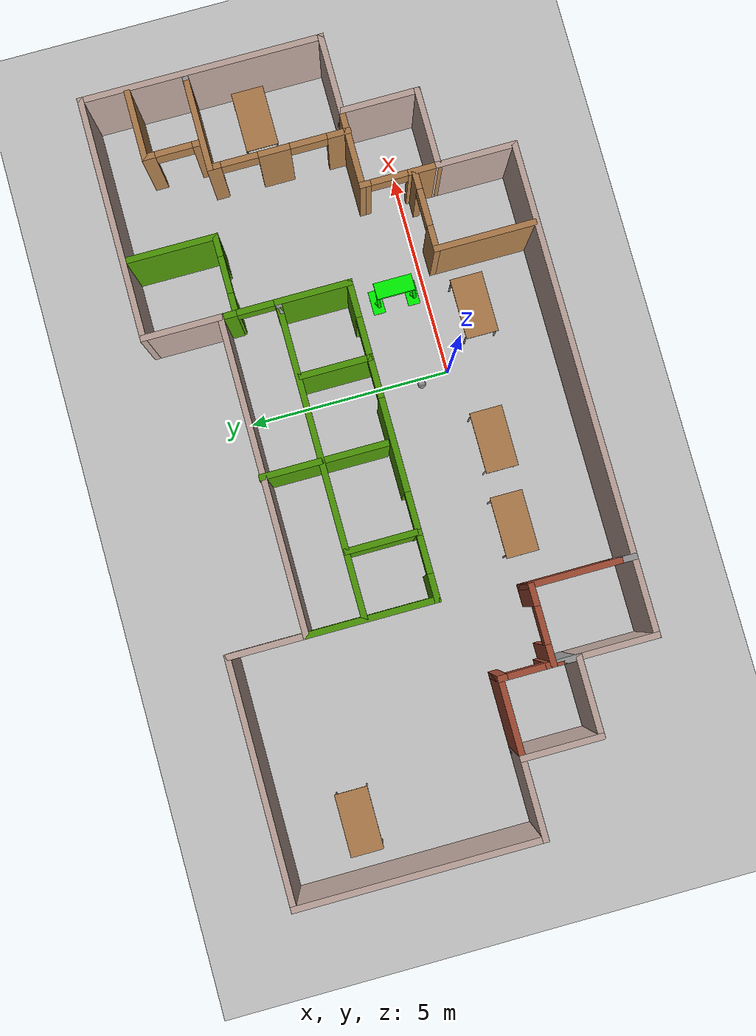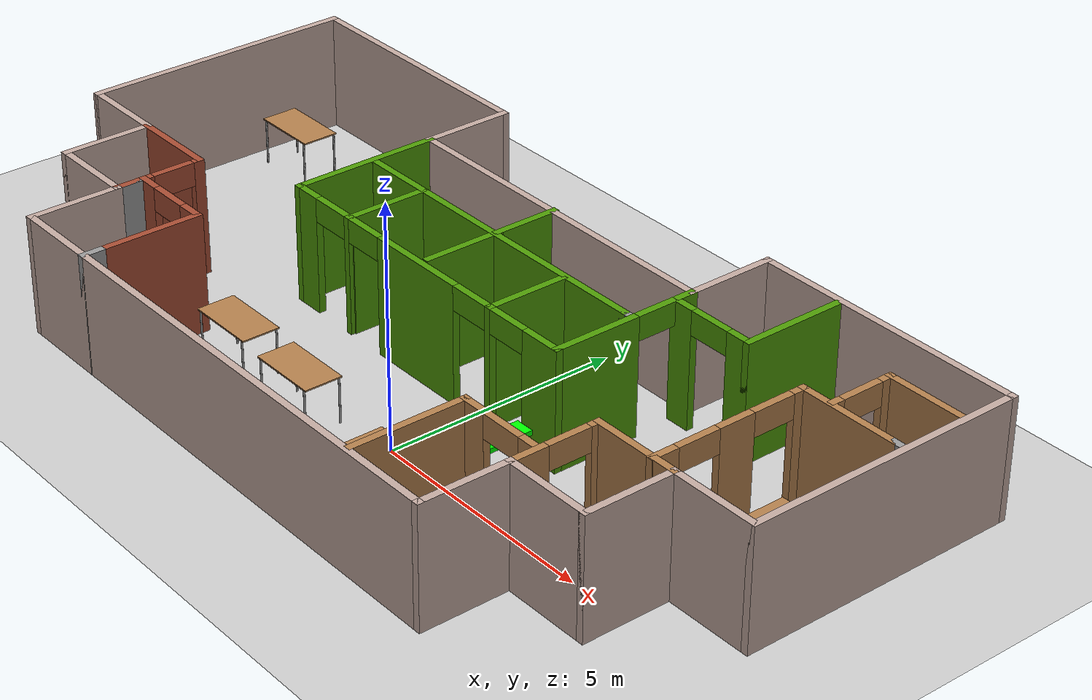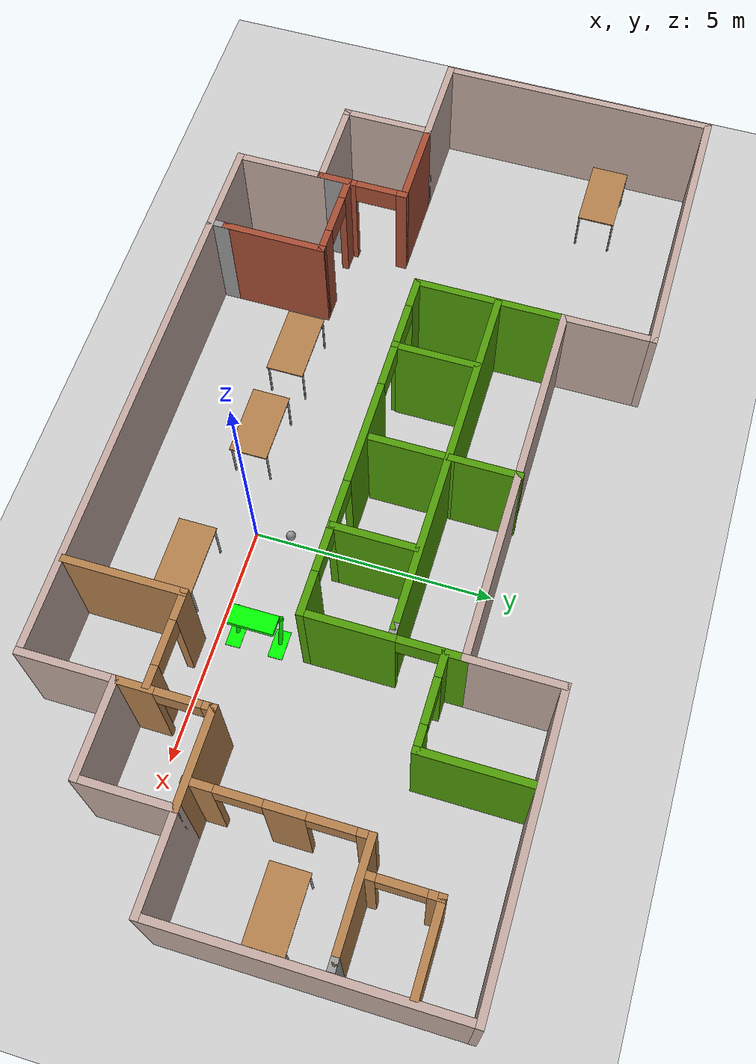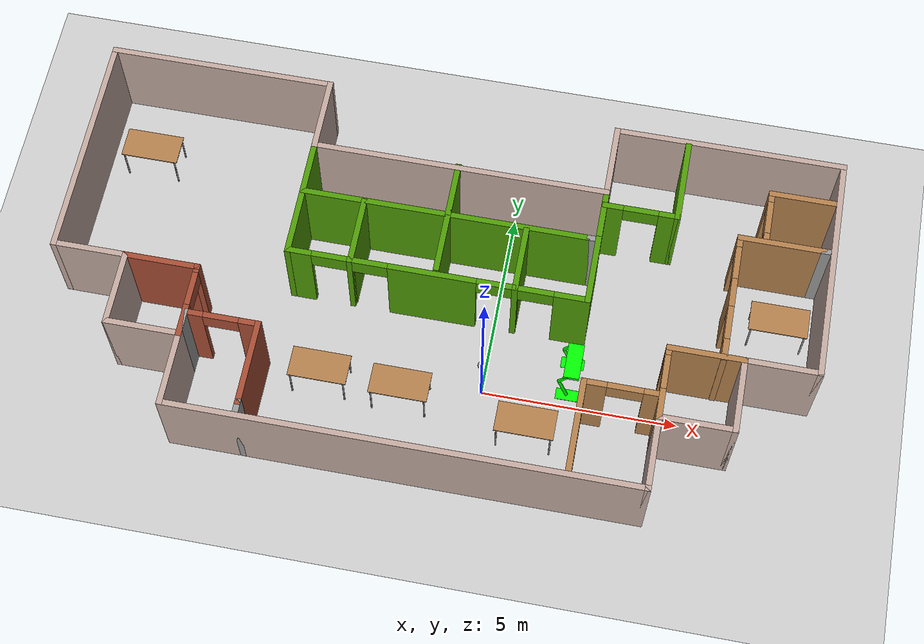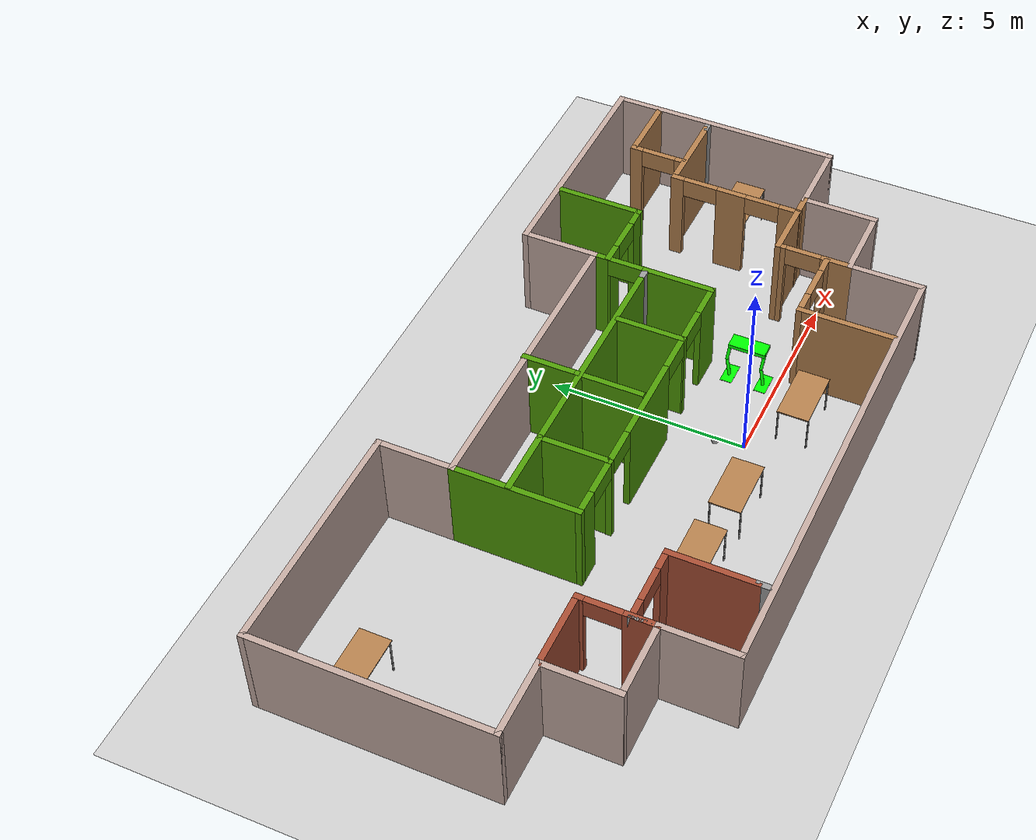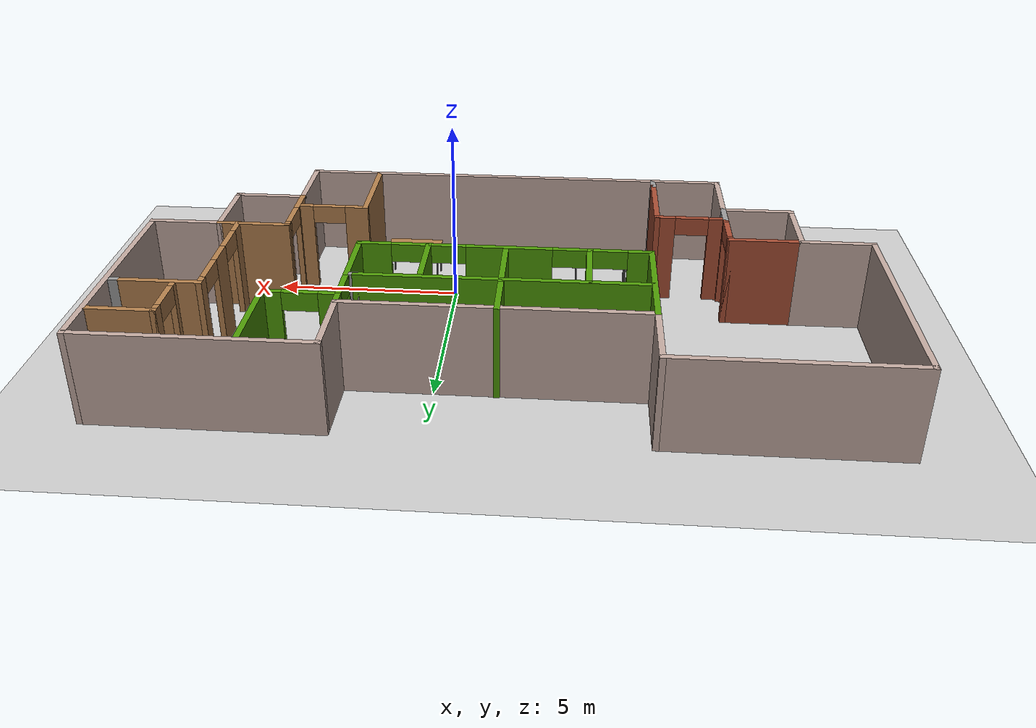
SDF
<sdf version="1.6">
 <world name="default">
  <plugin name="welcome_message" filename="libwelcome_message.so"/>
  <light name="sun" type="directional">
   <pose>0 0 10 0 -0 0</pose>
   <diffuse>0.8 0.8 0.8 1</diffuse>
   <specular>0.2 0.2 0.2 1</specular>
   <attenuation>
    <range>1000</range>
    <constant>0.9</constant>
    <linear>0.01</linear>
    <quadratic>0.001</quadratic>
   </attenuation>
   <direction>-0.5 0.1 -0.9</direction>
  </light>
  <model name="ground_plane">
   <static>1</static>
   <link name="link">
    <collision name="collision">
     <geometry><plane><normal>0 0 1</normal><size>100 100</size></plane></geometry>
     <surface>
      <contact><collide_bitmask>65535</collide_bitmask></contact>
      <friction><ode><mu>100</mu><mu2>50</mu2></ode></friction>
     </surface>
    </collision>
    <visual name="visual">
     <cast_shadows>0</cast_shadows>
     <geometry><plane><normal>0 0 1</normal><size>100 100</size></plane></geometry>
     <material>
      <script><uri>file://media/materials/scripts/gazebo.material</uri><name>Gazebo/Grey</name></script>
     </material>
    </visual>
   </link>
  </model>
  <gravity>0 0 -9.8</gravity>
  <magnetic_field>6e-06 2.3e-05 -4.2e-05</magnetic_field>
  <atmosphere type="adiabatic"/>
  <physics name="default_physics" default="0" type="ode">
   <max_step_size>0.001</max_step_size>
   <real_time_factor>1</real_time_factor>
   <real_time_update_rate>1000</real_time_update_rate>
  </physics>
  <scene><ambient>0.4 0.4 0.4 1</ambient><background>0.7 0.7 0.7 1</background><shadows>1</shadows></scene>
  <audio><device>default</device></audio>
  <spherical_coordinates>
   <surface_model>EARTH_WGS84</surface_model>
   <latitude_deg>0</latitude_deg>
   <longitude_deg>0</longitude_deg>
   <elevation>0</elevation>
   <heading_deg>0</heading_deg>
  </spherical_coordinates>
  <model name="robot_green1">
   <link name="link_1">
    <inertial>
     <mass>1</mass>
     <inertia>
      <ixx>0.166667</ixx>
      <ixy>0</ixy>
      <ixz>0</ixz>
      <iyy>0.166667</iyy>
      <iyz>0</iyz>
      <izz>0.166667</izz>
     </inertia>
    </inertial>
    <pose>0.108816 -0.448387 -0.328119 0 -0 0</pose>
    <visual name="visual">
     <geometry><box><size>0.6 0.3 0.01</size></box></geometry>
     <material>
      <lighting>1</lighting>
      <script><uri>file://media/materials/scripts/gazebo.material</uri><name>Gazebo/Grey</name></script>
      <shader type="vertex"><normal_map>__default__</normal_map></shader>
      <ambient>0 1 0 1</ambient>
      <diffuse>0.7 0.7 0.7 1</diffuse>
      <specular>0.01 0.01 0.01 1</specular>
      <emissive>0 0 0 1</emissive>
     </material>
    </visual>
    <collision name="collision">
     <geometry><box><size>0.6 0.3 0.01</size></box></geometry>
     <surface>
      <friction>
       <ode><mu>1</mu><mu2>1</mu2><fdir1>0 0 0</fdir1><slip1>0</slip1><slip2>0</slip2></ode>
       <torsional>
        <coefficient>1</coefficient>
        <patch_radius>0</patch_radius>
        <surface_radius>0</surface_radius>
        <use_patch_radius>1</use_patch_radius>
        <ode><slip>0</slip></ode>
       </torsional>
      </friction>
      <bounce><restitution_coefficient>0</restitution_coefficient><threshold>1e+06</threshold></bounce>
      <contact>
       <collide_without_contact>0</collide_without_contact>
       <collide_without_contact_bitmask>1</collide_without_contact_bitmask>
       <collide_bitmask>1</collide_bitmask>
       <ode>
        <soft_cfm>0</soft_cfm>
        <soft_erp>0.2</soft_erp>
        <kp>1e+13</kp>
        <kd>1</kd>
        <max_vel>0.01</max_vel>
        <min_depth>0</min_depth>
       </ode>
       <bullet>
        <split_impulse>1</split_impulse>
        <split_impulse_penetration_threshold>-0.01</split_impulse_penetration_threshold>
        <soft_cfm>0</soft_cfm>
        <soft_erp>0.2</soft_erp>
        <kp>1e+13</kp>
        <kd>1</kd>
       </bullet>
      </contact>
     </surface>
    </collision>
   </link>
   <link name="link_1_clone">
    <inertial>
     <mass>1</mass>
     <inertia>
      <ixx>0.166667</ixx>
      <ixy>0</ixy>
      <ixz>0</ixz>
      <iyy>0.166667</iyy>
      <iyz>0</iyz>
      <izz>0.166667</izz>
     </inertia>
    </inertial>
    <pose>0.108816 0.43723 -0.328119 0 -0 0</pose>
    <visual name="visual">
     <geometry><box><size>0.6 0.3 0.01</size></box></geometry>
     <material>
      <lighting>1</lighting>
      <script><uri>file://media/materials/scripts/gazebo.material</uri><name>Gazebo/Grey</name></script>
      <shader type="vertex"><normal_map>__default__</normal_map></shader>
      <ambient>0 1 0 1</ambient>
      <diffuse>0.7 0.7 0.7 1</diffuse>
      <specular>0.01 0.01 0.01 1</specular>
      <emissive>0 0 0 1</emissive>
     </material>
    </visual>
    <collision name="collision">
     <geometry><box><size>0.6 0.3 0.01</size></box></geometry>
     <surface>
      <friction>
       <ode><mu>1</mu><mu2>1</mu2><fdir1>0 0 0</fdir1><slip1>0</slip1><slip2>0</slip2></ode>
       <torsional>
        <coefficient>1</coefficient>
        <patch_radius>0</patch_radius>
        <surface_radius>0</surface_radius>
        <use_patch_radius>1</use_patch_radius>
        <ode><slip>0</slip></ode>
       </torsional>
      </friction>
      <bounce><restitution_coefficient>0</restitution_coefficient><threshold>1e+06</threshold></bounce>
      <contact>
       <collide_without_contact>0</collide_without_contact>
       <collide_without_contact_bitmask>1</collide_without_contact_bitmask>
       <collide_bitmask>1</collide_bitmask>
       <ode>
        <soft_cfm>0</soft_cfm>
        <soft_erp>0.2</soft_erp>
        <kp>1e+13</kp>
        <kd>1</kd>
        <max_vel>0.01</max_vel>
        <min_depth>0</min_depth>
       </ode>
       <bullet>
        <split_impulse>1</split_impulse>
        <split_impulse_penetration_threshold>-0.01</split_impulse_penetration_threshold>
        <soft_cfm>0</soft_cfm>
        <soft_erp>0.2</soft_erp>
        <kp>1e+13</kp>
        <kd>1</kd>
       </bullet>
      </contact>
     </surface>
    </collision>
   </link>
   <link name="link_2">
    <inertial>
     <mass>1</mass>
     <inertia><ixx>0.145833</ixx><ixy>0</ixy><ixz>0</ixz><iyy>0.145833</iyy><iyz>0</iyz><izz>0.125</izz></inertia>
    </inertial>
    <pose>0.083446 -0.438387 -0.316611 0 -0.3 0</pose>
    <visual name="visual">
     <pose>0 0 0.4 0 -0 0</pose>
     <geometry><cylinder><radius>0.04</radius><length>0.8</length></cylinder></geometry>
     <material>
      <lighting>1</lighting>
      <script><uri>file://media/materials/scripts/gazebo.material</uri><name>Gazebo/Grey</name></script>
      <shader type="vertex"><normal_map>__default__</normal_map></shader>
      <ambient>0 1 0 1</ambient>
      <diffuse>0.7 0.7 0.7 1</diffuse>
      <specular>0.01 0.01 0.01 1</specular>
      <emissive>0 0 0 1</emissive>
     </material>
    </visual>
    <collision name="collision">
     <pose>0 0 0.4 0 -0 0</pose>
     <geometry><cylinder><radius>0.04</radius><length>0.8</length></cylinder></geometry>
     <surface>
      <friction>
       <ode><mu>1</mu><mu2>1</mu2><fdir1>0 0 0</fdir1><slip1>0</slip1><slip2>0</slip2></ode>
       <torsional>
        <coefficient>1</coefficient>
        <patch_radius>0</patch_radius>
        <surface_radius>0</surface_radius>
        <use_patch_radius>1</use_patch_radius>
        <ode><slip>0</slip></ode>
       </torsional>
      </friction>
      <bounce><restitution_coefficient>0</restitution_coefficient><threshold>1e+06</threshold></bounce>
      <contact>
       <collide_without_contact>0</collide_without_contact>
       <collide_without_contact_bitmask>1</collide_without_contact_bitmask>
       <collide_bitmask>1</collide_bitmask>
       <ode>
        <soft_cfm>0</soft_cfm>
        <soft_erp>0.2</soft_erp>
        <kp>1e+13</kp>
        <kd>1</kd>
        <max_vel>0.01</max_vel>
        <min_depth>0</min_depth>
       </ode>
       <bullet>
        <split_impulse>1</split_impulse>
        <split_impulse_penetration_threshold>-0.01</split_impulse_penetration_threshold>
        <soft_cfm>0</soft_cfm>
        <soft_erp>0.2</soft_erp>
        <kp>1e+13</kp>
        <kd>1</kd>
       </bullet>
      </contact>
     </surface>
    </collision>
   </link>
   <link name="link_2_clone">
    <inertial>
     <mass>1</mass>
     <inertia><ixx>0.145833</ixx><ixy>0</ixy><ixz>0</ixz><iyy>0.145833</iyy><iyz>0</iyz><izz>0.125</izz></inertia>
    </inertial>
    <pose>-0.26733 -0.444034 0.261881 0 0.58 0</pose>
    <visual name="visual">
     <pose>0 0 0.4 0 -0 0</pose>
     <geometry><cylinder><radius>0.04</radius><length>0.4</length></cylinder></geometry>
     <material>
      <lighting>1</lighting>
      <script><uri>file://media/materials/scripts/gazebo.material</uri><name>Gazebo/Grey</name></script>
      <shader type="vertex"><normal_map>__default__</normal_map></shader>
      <ambient>0 1 0 1</ambient>
      <diffuse>0.7 0.7 0.7 1</diffuse>
      <specular>0.01 0.01 0.01 1</specular>
      <emissive>0 0 0 1</emissive>
     </material>
    </visual>
    <collision name="collision">
     <pose>0 0 0.4 0 -0 0</pose>
     <geometry><cylinder><radius>0.04</radius><length>0.4</length></cylinder></geometry>
     <surface>
      <friction>
       <ode><mu>1</mu><mu2>1</mu2><fdir1>0 0 0</fdir1><slip1>0</slip1><slip2>0</slip2></ode>
       <torsional>
        <coefficient>1</coefficient>
        <patch_radius>0</patch_radius>
        <surface_radius>0</surface_radius>
        <use_patch_radius>1</use_patch_radius>
        <ode><slip>0</slip></ode>
       </torsional>
      </friction>
      <bounce><restitution_coefficient>0</restitution_coefficient><threshold>1e+06</threshold></bounce>
      <contact>
       <collide_without_contact>0</collide_without_contact>
       <collide_without_contact_bitmask>1</collide_without_contact_bitmask>
       <collide_bitmask>1</collide_bitmask>
       <ode>
        <soft_cfm>0</soft_cfm>
        <soft_erp>0.2</soft_erp>
        <kp>1e+13</kp>
        <kd>1</kd>
        <max_vel>0.01</max_vel>
        <min_depth>0</min_depth>
       </ode>
       <bullet>
        <split_impulse>1</split_impulse>
        <split_impulse_penetration_threshold>-0.01</split_impulse_penetration_threshold>
        <soft_cfm>0</soft_cfm>
        <soft_erp>0.2</soft_erp>
        <kp>1e+13</kp>
        <kd>1</kd>
       </bullet>
      </contact>
     </surface>
    </collision>
   </link>
   <link name="link_2_clone_0">
    <inertial>
     <mass>1</mass>
     <inertia><ixx>0.145833</ixx><ixy>0</ixy><ixz>0</ixz><iyy>0.145833</iyy><iyz>0</iyz><izz>0.125</izz></inertia>
    </inertial>
    <pose>0.083446 0.446613 -0.316611 0 -0.3 0</pose>
    <visual name="visual">
     <pose>0 0 0.4 0 -0 0</pose>
     <geometry><cylinder><radius>0.04</radius><length>0.8</length></cylinder></geometry>
     <material>
      <lighting>1</lighting>
      <script><uri>file://media/materials/scripts/gazebo.material</uri><name>Gazebo/Grey</name></script>
      <shader type="vertex"><normal_map>__default__</normal_map></shader>
      <ambient>0 1 0 1</ambient>
      <diffuse>0.7 0.7 0.7 1</diffuse>
      <specular>0.01 0.01 0.01 1</specular>
      <emissive>0 0 0 1</emissive>
     </material>
    </visual>
    <collision name="collision">
     <pose>0 0 0.4 0 -0 0</pose>
     <geometry><cylinder><radius>0.04</radius><length>0.8</length></cylinder></geometry>
     <surface>
      <friction>
       <ode><mu>1</mu><mu2>1</mu2><fdir1>0 0 0</fdir1><slip1>0</slip1><slip2>0</slip2></ode>
       <torsional>
        <coefficient>1</coefficient>
        <patch_radius>0</patch_radius>
        <surface_radius>0</surface_radius>
        <use_patch_radius>1</use_patch_radius>
        <ode><slip>0</slip></ode>
       </torsional>
      </friction>
      <bounce><restitution_coefficient>0</restitution_coefficient><threshold>1e+06</threshold></bounce>
      <contact>
       <collide_without_contact>0</collide_without_contact>
       <collide_without_contact_bitmask>1</collide_without_contact_bitmask>
       <collide_bitmask>1</collide_bitmask>
       <ode>
        <soft_cfm>0</soft_cfm>
        <soft_erp>0.2</soft_erp>
        <kp>1e+13</kp>
        <kd>1</kd>
        <max_vel>0.01</max_vel>
        <min_depth>0</min_depth>
       </ode>
       <bullet>
        <split_impulse>1</split_impulse>
        <split_impulse_penetration_threshold>-0.01</split_impulse_penetration_threshold>
        <soft_cfm>0</soft_cfm>
        <soft_erp>0.2</soft_erp>
        <kp>1e+13</kp>
        <kd>1</kd>
       </bullet>
      </contact>
     </surface>
    </collision>
   </link>
   <link name="link_2_clone_clone">
    <inertial>
     <mass>1</mass>
     <inertia><ixx>0.145833</ixx><ixy>0</ixy><ixz>0</ixz><iyy>0.145833</iyy><iyz>0</iyz><izz>0.125</izz></inertia>
    </inertial>
    <pose>-0.26733 0.446613 0.261881 0 0.58 0</pose>
    <visual name="visual">
     <pose>0 0 0.4 0 -0 0</pose>
     <geometry><cylinder><radius>0.04</radius><length>0.4</length></cylinder></geometry>
     <material>
      <lighting>1</lighting>
      <script><uri>file://media/materials/scripts/gazebo.material</uri><name>Gazebo/Grey</name></script>
      <shader type="vertex"><normal_map>__default__</normal_map></shader>
      <ambient>0 1 0 1</ambient>
      <diffuse>0.7 0.7 0.7 1</diffuse>
      <specular>0.01 0.01 0.01 1</specular>
      <emissive>0 0 0 1</emissive>
     </material>
    </visual>
    <collision name="collision">
     <pose>0 0 0.4 0 -0 0</pose>
     <geometry><cylinder><radius>0.04</radius><length>0.4</length></cylinder></geometry>
     <surface>
      <friction>
       <ode><mu>1</mu><mu2>1</mu2><fdir1>0 0 0</fdir1><slip1>0</slip1><slip2>0</slip2></ode>
       <torsional>
        <coefficient>1</coefficient>
        <patch_radius>0</patch_radius>
        <surface_radius>0</surface_radius>
        <use_patch_radius>1</use_patch_radius>
        <ode><slip>0</slip></ode>
       </torsional>
      </friction>
      <bounce><restitution_coefficient>0</restitution_coefficient><threshold>1e+06</threshold></bounce>
      <contact>
       <collide_without_contact>0</collide_without_contact>
       <collide_without_contact_bitmask>1</collide_without_contact_bitmask>
       <collide_bitmask>1</collide_bitmask>
       <ode>
        <soft_cfm>0</soft_cfm>
        <soft_erp>0.2</soft_erp>
        <kp>1e+13</kp>
        <kd>1</kd>
        <max_vel>0.01</max_vel>
        <min_depth>0</min_depth>
       </ode>
       <bullet>
        <split_impulse>1</split_impulse>
        <split_impulse_penetration_threshold>-0.01</split_impulse_penetration_threshold>
        <soft_cfm>0</soft_cfm>
        <soft_erp>0.2</soft_erp>
        <kp>1e+13</kp>
        <kd>1</kd>
       </bullet>
      </contact>
     </surface>
    </collision>
   </link>
   <link name="link_3">
    <inertial>
     <mass>1</mass>
     <inertia>
      <ixx>0.166667</ixx>
      <ixy>0</ixy>
      <ixz>0</ixz>
      <iyy>0.166667</iyy>
      <iyz>0</iyz>
      <izz>0.166667</izz>
     </inertia>
    </inertial>
    <pose>0.150138 0.000351 0.765701 0 -0 0</pose>
    <visual name="visual">
     <geometry><box><size>0.4 0.95 0.1</size></box></geometry>
     <material>
      <lighting>1</lighting>
      <script><uri>file://media/materials/scripts/gazebo.material</uri><name>Gazebo/Grey</name></script>
      <shader type="vertex"><normal_map>__default__</normal_map></shader>
      <ambient>0 1 0 1</ambient>
      <diffuse>0.7 0.7 0.7 1</diffuse>
      <specular>0.01 0.01 0.01 1</specular>
      <emissive>0 0 0 1</emissive>
     </material>
    </visual>
    <collision name="collision">
     <geometry><box><size>0.4 0.95 0.1</size></box></geometry>
     <surface>
      <friction>
       <ode><mu>1</mu><mu2>1</mu2><fdir1>0 0 0</fdir1><slip1>0</slip1><slip2>0</slip2></ode>
       <torsional>
        <coefficient>1</coefficient>
        <patch_radius>0</patch_radius>
        <surface_radius>0</surface_radius>
        <use_patch_radius>1</use_patch_radius>
        <ode><slip>0</slip></ode>
       </torsional>
      </friction>
      <bounce><restitution_coefficient>0</restitution_coefficient><threshold>1e+06</threshold></bounce>
      <contact>
       <collide_without_contact>0</collide_without_contact>
       <collide_without_contact_bitmask>1</collide_without_contact_bitmask>
       <collide_bitmask>1</collide_bitmask>
       <ode>
        <soft_cfm>0</soft_cfm>
        <soft_erp>0.2</soft_erp>
        <kp>1e+13</kp>
        <kd>1</kd>
        <max_vel>0.01</max_vel>
        <min_depth>0</min_depth>
       </ode>
       <bullet>
        <split_impulse>1</split_impulse>
        <split_impulse_penetration_threshold>-0.01</split_impulse_penetration_threshold>
        <soft_cfm>0</soft_cfm>
        <soft_erp>0.2</soft_erp>
        <kp>1e+13</kp>
        <kd>1</kd>
       </bullet>
      </contact>
     </surface>
    </collision>
   </link>
   <joint name="link_1_JOINT_0" type="revolute">
    <parent>link_1</parent>
    <child>link_2</child>
    <axis>
     <xyz>0 0 1</xyz>
     <use_parent_model_frame>0</use_parent_model_frame>
     <limit>
      <lower>-1.79769e+308</lower>
      <upper>1.79769e+308</upper>
      <effort>-1</effort>
      <velocity>-1</velocity>
     </limit>
     <dynamics>
      <spring_reference>0</spring_reference>
      <spring_stiffness>0</spring_stiffness>
      <damping>0</damping>
     </dynamics>
    </axis>
    <physics>
     <ode><limit><cfm>0</cfm><erp>0.2</erp></limit><suspension><cfm>0</cfm><erp>0.2</erp></suspension></ode>
    </physics>
   </joint>
   <joint name="link_1_clone_JOINT_2" type="revolute">
    <parent>link_1_clone</parent>
    <child>link_2_clone_0</child>
    <axis>
     <xyz>0 0 1</xyz>
     <use_parent_model_frame>0</use_parent_model_frame>
     <limit>
      <lower>-1.79769e+308</lower>
      <upper>1.79769e+308</upper>
      <effort>-1</effort>
      <velocity>-1</velocity>
     </limit>
     <dynamics>
      <spring_reference>0</spring_reference>
      <spring_stiffness>0</spring_stiffness>
      <damping>0</damping>
     </dynamics>
    </axis>
    <physics>
     <ode><limit><cfm>0</cfm><erp>0.2</erp></limit><suspension><cfm>0</cfm><erp>0.2</erp></suspension></ode>
    </physics>
   </joint>
   <joint name="link_2_JOINT_1" type="revolute">
    <parent>link_2</parent>
    <child>link_2_clone</child>
    <axis>
     <xyz>0 0 1</xyz>
     <use_parent_model_frame>0</use_parent_model_frame>
     <limit>
      <lower>-1.79769e+308</lower>
      <upper>1.79769e+308</upper>
      <effort>-1</effort>
      <velocity>-1</velocity>
     </limit>
     <dynamics>
      <spring_reference>0</spring_reference>
      <spring_stiffness>0</spring_stiffness>
      <damping>0</damping>
     </dynamics>
    </axis>
    <physics>
     <ode><limit><cfm>0</cfm><erp>0.2</erp></limit><suspension><cfm>0</cfm><erp>0.2</erp></suspension></ode>
    </physics>
   </joint>
   <joint name="link_2_clone_0_JOINT_3" type="revolute">
    <parent>link_2_clone_0</parent>
    <child>link_2_clone_clone</child>
    <axis>
     <xyz>0 0 1</xyz>
     <use_parent_model_frame>0</use_parent_model_frame>
     <limit>
      <lower>-1.79769e+308</lower>
      <upper>1.79769e+308</upper>
      <effort>-1</effort>
      <velocity>-1</velocity>
     </limit>
     <dynamics>
      <spring_reference>0</spring_reference>
      <spring_stiffness>0</spring_stiffness>
      <damping>0</damping>
     </dynamics>
    </axis>
    <physics>
     <ode><limit><cfm>0</cfm><erp>0.2</erp></limit><suspension><cfm>0</cfm><erp>0.2</erp></suspension></ode>
    </physics>
   </joint>
   <joint name="link_3_JOINT_4" type="revolute">
    <parent>link_3</parent>
    <child>link_2_clone</child>
    <axis>
     <xyz>0 0 1</xyz>
     <use_parent_model_frame>0</use_parent_model_frame>
     <limit>
      <lower>-1.79769e+308</lower>
      <upper>1.79769e+308</upper>
      <effort>-1</effort>
      <velocity>-1</velocity>
     </limit>
     <dynamics>
      <spring_reference>0</spring_reference>
      <spring_stiffness>0</spring_stiffness>
      <damping>0</damping>
     </dynamics>
    </axis>
    <physics>
     <ode><limit><cfm>0</cfm><erp>0.2</erp></limit><suspension><cfm>0</cfm><erp>0.2</erp></suspension></ode>
    </physics>
   </joint>
   <joint name="link_3_JOINT_7" type="revolute">
    <parent>link_3</parent>
    <child>link_2_clone_clone</child>
    <axis>
     <xyz>0 0 1</xyz>
     <use_parent_model_frame>0</use_parent_model_frame>
     <limit>
      <lower>-1.79769e+308</lower>
      <upper>1.79769e+308</upper>
      <effort>-1</effort>
      <velocity>-1</velocity>
     </limit>
     <dynamics>
      <spring_reference>0</spring_reference>
      <spring_stiffness>0</spring_stiffness>
      <damping>0</damping>
     </dynamics>
    </axis>
    <physics>
     <ode><limit><cfm>0</cfm><erp>0.2</erp></limit><suspension><cfm>0</cfm><erp>0.2</erp></suspension></ode>
    </physics>
   </joint>
   <static>0</static>
   <pose>2.04376 0.790472 0.333119 0 -0 0.001173</pose>
  </model>
  <model name="office">
   <pose>-1.48529 2.04777 0 0 -0 0</pose>
   <link name="Wall_10">
    <collision name="Wall_10_Collision">
     <geometry><box><size>2 0.15 2.5</size></box></geometry>
     <pose>0 0 1.25 0 -0 0</pose>
    </collision>
    <visual name="Wall_10_Visual">
     <pose>0 0 1.25 0 -0 0</pose>
     <geometry><box><size>2 0.15 2.5</size></box></geometry>
     <material>
      <script><uri>file://media/materials/scripts/gazebo.material</uri><name>Gazebo/Grey</name></script>
      <ambient>0.760784 0.662745 0.627451 1</ambient>
     </material>
     <meta><layer>0</layer></meta>
    </visual>
    <pose>6.85 -2.925 0 0 -0 0</pose>
   </link>
   <link name="Wall_11">
    <collision name="Wall_11_Collision">
     <geometry><box><size>2 0.15 2.5</size></box></geometry>
     <pose>0 0 1.25 0 -0 0</pose>
    </collision>
    <visual name="Wall_11_Visual">
     <pose>0 0 1.25 0 -0 0</pose>
     <geometry><box><size>2 0.15 2.5</size></box></geometry>
     <material>
      <script><uri>file://media/materials/scripts/gazebo.material</uri><name>Gazebo/Grey</name></script>
      <ambient>0.760784 0.662745 0.627451 1</ambient>
     </material>
     <meta><layer>0</layer></meta>
    </visual>
    <pose>7.775 -2 0 0 -0 1.5708</pose>
   </link>
   <link name="Wall_12">
    <collision name="Wall_12_Collision">
     <geometry><box><size>2 0.15 2.5</size></box></geometry>
     <pose>0 0 1.25 0 -0 0</pose>
    </collision>
    <visual name="Wall_12_Visual">
     <pose>0 0 1.25 0 -0 0</pose>
     <geometry><box><size>2 0.15 2.5</size></box></geometry>
     <material>
      <script><uri>file://media/materials/scripts/gazebo.material</uri><name>Gazebo/Grey</name></script>
      <ambient>0.760784 0.662745 0.627451 1</ambient>
     </material>
     <meta><layer>0</layer></meta>
    </visual>
    <pose>8.7 -1.075 0 0 -0 0</pose>
   </link>
   <link name="Wall_13">
    <collision name="Wall_13_Collision">
     <geometry><box><size>6 0.15 2.5</size></box></geometry>
     <pose>0 0 1.25 0 -0 0</pose>
    </collision>
    <visual name="Wall_13_Visual">
     <pose>0 0 1.25 0 -0 0</pose>
     <geometry><box><size>6 0.15 2.5</size></box></geometry>
     <material>
      <script><uri>file://media/materials/scripts/gazebo.material</uri><name>Gazebo/Grey</name></script>
      <ambient>0.760784 0.662745 0.627451 1</ambient>
     </material>
     <meta><layer>0</layer></meta>
    </visual>
    <pose>9.625 1.85 0 0 -0 1.5708</pose>
   </link>
   <link name="Wall_14">
    <collision name="Wall_14_Collision">
     <geometry><box><size>6 0.15 2.5</size></box></geometry>
     <pose>0 0 1.25 0 -0 0</pose>
    </collision>
    <visual name="Wall_14_Visual">
     <pose>0 0 1.25 0 -0 0</pose>
     <geometry><box><size>6 0.15 2.5</size></box></geometry>
     <material>
      <script><uri>file://media/materials/scripts/gazebo.material</uri><name>Gazebo/Grey</name></script>
      <ambient>0.760784 0.662745 0.627451 1</ambient>
     </material>
     <meta><layer>0</layer></meta>
    </visual>
    <pose>6.7 4.775 0 0 -0 3.14159</pose>
   </link>
   <link name="Wall_15">
    <collision name="Wall_15_Collision">
     <geometry><box><size>2 0.15 2.5</size></box></geometry>
     <pose>0 0 1.25 0 -0 0</pose>
    </collision>
    <visual name="Wall_15_Visual">
     <pose>0 0 1.25 0 -0 0</pose>
     <geometry><box><size>2 0.15 2.5</size></box></geometry>
     <material>
      <script><uri>file://media/materials/scripts/gazebo.material</uri><name>Gazebo/Grey</name></script>
      <ambient>0.760784 0.662745 0.627451 1</ambient>
     </material>
     <meta><layer>0</layer></meta>
    </visual>
    <pose>3.775 3.85 0 0 -0 -1.5708</pose>
   </link>
   <link name="Wall_16">
    <collision name="Wall_16_Collision">
     <geometry><box><size>7.75 0.15 2.5</size></box></geometry>
     <pose>0 0 1.25 0 -0 0</pose>
    </collision>
    <visual name="Wall_16_Visual">
     <pose>0 0 1.25 0 -0 0</pose>
     <geometry><box><size>7.75 0.15 2.5</size></box></geometry>
     <material>
      <script><uri>file://media/materials/scripts/gazebo.material</uri><name>Gazebo/Grey</name></script>
      <ambient>0.760784 0.662745 0.627451 1</ambient>
     </material>
     <meta><layer>0</layer></meta>
    </visual>
    <pose>-0.025 2.925 0 0 -0 3.14159</pose>
   </link>
   <link name="Wall_17">
    <collision name="Wall_17_Collision">
     <geometry><box><size>2 0.15 2.5</size></box></geometry>
     <pose>0 0 1.25 0 -0 0</pose>
    </collision>
    <visual name="Wall_17_Visual">
     <pose>0 0 1.25 0 -0 0</pose>
     <geometry><box><size>2 0.15 2.5</size></box></geometry>
     <material>
      <script><uri>file://media/materials/scripts/gazebo.material</uri><name>Gazebo/Grey</name></script>
      <ambient>0.760784 0.662745 0.627451 1</ambient>
     </material>
     <meta><layer>0</layer></meta>
    </visual>
    <pose>-3.825 3.85 0 0 -0 1.5708</pose>
   </link>
   <link name="Wall_18">
    <collision name="Wall_18_Collision">
     <geometry><box><size>5.95 0.15 2.5</size></box></geometry>
     <pose>0 0 1.25 0 -0 0</pose>
    </collision>
    <visual name="Wall_18_Visual">
     <pose>0 0 1.25 0 -0 0</pose>
     <geometry><box><size>5.95 0.15 2.5</size></box></geometry>
     <material>
      <script><uri>file://media/materials/scripts/gazebo.material</uri><name>Gazebo/Grey</name></script>
      <ambient>0.760784 0.662745 0.627451 1</ambient>
     </material>
     <meta><layer>0</layer></meta>
    </visual>
    <pose>-6.725 4.775 0 0 -0 3.14159</pose>
   </link>
   <link name="Wall_19">
    <collision name="Wall_19_Collision">
     <geometry><box><size>0.15 0.15 2.5</size></box></geometry>
     <pose>0 0 1.25 0 -0 0</pose>
    </collision>
    <visual name="Wall_19_Visual">
     <pose>0 0 1.25 0 -0 0</pose>
     <geometry><box><size>0.15 0.15 2.5</size></box></geometry>
     <material>
      <script><uri>file://media/materials/scripts/gazebo.material</uri><name>Gazebo/Grey</name></script>
      <ambient>0.760784 0.662745 0.627451 1</ambient>
     </material>
     <meta><layer>0</layer></meta>
    </visual>
    <pose>-9.625 4.775 0 0 -0 0</pose>
   </link>
   <link name="Wall_2">
    <collision name="Wall_2_Collision">
     <geometry><box><size>6 0.15 2.5</size></box></geometry>
     <pose>0 0 1.25 0 -0 0</pose>
    </collision>
    <visual name="Wall_2_Visual">
     <pose>0 0 1.25 0 -0 0</pose>
     <geometry><box><size>6 0.15 2.5</size></box></geometry>
     <material>
      <script><uri>file://media/materials/scripts/gazebo.material</uri><name>Gazebo/Grey</name></script>
      <ambient>0.760784 0.662745 0.627451 1</ambient>
     </material>
     <meta><layer>0</layer></meta>
    </visual>
    <pose>-9.625 1.85 0 0 -0 -1.5708</pose>
   </link>
   <link name="Wall_21">
    <collision name="Wall_21_Collision">
     <geometry><box><size>2 0.15 2.5</size></box></geometry>
     <pose>0 0 1.25 0 -0 0</pose>
    </collision>
    <visual name="Wall_21_Visual">
     <pose>0 0 1.25 0 -0 0</pose>
     <geometry><box><size>2 0.15 2.5</size></box></geometry>
     <material>
      <script><uri>file://media/materials/scripts/gazebo.material</uri><name>Gazebo/Bricks</name></script>
      <ambient>1 0.764706 0.305882 1</ambient>
     </material>
     <meta><layer>0</layer></meta>
    </visual>
    <pose>-6.85 -1.075 0 0 -0 0</pose>
   </link>
   <link name="Wall_22">
    <pose>-5.925 -2 0 0 -0 -1.5708</pose>
    <visual name="Wall_22_Visual_0">
     <pose>-0.880847 0 1.25 0 -0 0</pose>
     <geometry><box><size>0.238307 0.15 2.5</size></box></geometry>
     <material>
      <script><uri>file://media/materials/scripts/gazebo.material</uri><name>Gazebo/Bricks</name></script>
      <ambient>1 0.764706 0.305882 1</ambient>
     </material>
     <meta><layer>0</layer></meta>
    </visual>
    <collision name="Wall_22_Collision_0">
     <geometry><box><size>0.238307 0.15 2.5</size></box></geometry>
     <pose>-0.880847 0 1.25 0 -0 0</pose>
    </collision>
    <visual name="Wall_22_Visual_1">
     <pose>0.569153 0 1.25 0 -0 0</pose>
     <geometry><box><size>0.861693 0.15 2.5</size></box></geometry>
     <material>
      <script><uri>file://media/materials/scripts/gazebo.material</uri><name>Gazebo/Bricks</name></script>
      <ambient>1 0.764706 0.305882 1</ambient>
     </material>
     <meta><layer>0</layer></meta>
    </visual>
    <collision name="Wall_22_Collision_1">
     <geometry><box><size>0.861693 0.15 2.5</size></box></geometry>
     <pose>0.569153 0 1.25 0 -0 0</pose>
    </collision>
    <visual name="Wall_22_Visual_2">
     <pose>-0.311693 0 2.25 0 -0 0</pose>
     <geometry><box><size>0.9 0.15 0.5</size></box></geometry>
     <material>
      <script><uri>file://media/materials/scripts/gazebo.material</uri><name>Gazebo/Bricks</name></script>
      <ambient>1 0.764706 0.305882 1</ambient>
     </material>
     <meta><layer>0</layer></meta>
    </visual>
    <collision name="Wall_22_Collision_2">
     <geometry><box><size>0.9 0.15 0.5</size></box></geometry>
     <pose>-0.311693 0 2.25 0 -0 0</pose>
    </collision>
   </link>
   <link name="Wall_23">
    <collision name="Wall_23_Collision">
     <geometry><box><size>0.75 0.15 2.5</size></box></geometry>
     <pose>0 0 1.25 0 -0 0</pose>
    </collision>
    <visual name="Wall_23_Visual">
     <pose>0 0 1.25 0 -0 0</pose>
     <geometry><box><size>0.75 0.15 2.5</size></box></geometry>
     <material>
      <script><uri>file://media/materials/scripts/gazebo.material</uri><name>Gazebo/Grey</name></script>
      <ambient>1 1 1 1</ambient>
     </material>
     <meta><layer>0</layer></meta>
    </visual>
    <pose>-5.925 -2.625 0 0 -0 1.5708</pose>
   </link>
   <link name="Wall_24">
    <pose>-5 -2.325 0 0 -0 0</pose>
    <visual name="Wall_24_Visual_0">
     <pose>-0.733979 0 1.25 0 -0 0</pose>
     <geometry><box><size>0.532042 0.15 2.5</size></box></geometry>
     <material>
      <script><uri>file://media/materials/scripts/gazebo.material</uri><name>Gazebo/Bricks</name></script>
      <ambient>1 0.764706 0.305882 1</ambient>
     </material>
     <meta><layer>0</layer></meta>
    </visual>
    <collision name="Wall_24_Collision_0">
     <geometry><box><size>0.532042 0.15 2.5</size></box></geometry>
     <pose>-0.733979 0 1.25 0 -0 0</pose>
    </collision>
    <visual name="Wall_24_Visual_1">
     <pose>0.716021 0 1.25 0 -0 0</pose>
     <geometry><box><size>0.567958 0.15 2.5</size></box></geometry>
     <material>
      <script><uri>file://media/materials/scripts/gazebo.material</uri><name>Gazebo/Bricks</name></script>
      <ambient>1 0.764706 0.305882 1</ambient>
     </material>
     <meta><layer>0</layer></meta>
    </visual>
    <collision name="Wall_24_Collision_1">
     <geometry><box><size>0.567958 0.15 2.5</size></box></geometry>
     <pose>0.716021 0 1.25 0 -0 0</pose>
    </collision>
    <visual name="Wall_24_Visual_2">
     <pose>-0.017958 0 2.25 0 -0 0</pose>
     <geometry><box><size>0.9 0.15 0.5</size></box></geometry>
     <material>
      <script><uri>file://media/materials/scripts/gazebo.material</uri><name>Gazebo/Bricks</name></script>
      <ambient>1 0.764706 0.305882 1</ambient>
     </material>
     <meta><layer>0</layer></meta>
    </visual>
    <collision name="Wall_24_Collision_2">
     <geometry><box><size>0.9 0.15 0.5</size></box></geometry>
     <pose>-0.017958 0 2.25 0 -0 0</pose>
    </collision>
   </link>
   <link name="Wall_25">
    <collision name="Wall_25_Collision">
     <geometry><box><size>2.25 0.15 2.5</size></box></geometry>
     <pose>0 0 1.25 0 -0 0</pose>
    </collision>
    <visual name="Wall_25_Visual">
     <pose>0 0 1.25 0 -0 0</pose>
     <geometry><box><size>2.25 0.15 2.5</size></box></geometry>
     <material>
      <script><uri>file://media/materials/scripts/gazebo.material</uri><name>Gazebo/Bricks</name></script>
      <ambient>1 0.764706 0.305882 1</ambient>
     </material>
     <meta><layer>0</layer></meta>
    </visual>
    <pose>-4.075 -3.375 0 0 -0 -1.5708</pose>
   </link>
   <link name="Wall_26">
    <collision name="Wall_26_Collision">
     <geometry><box><size>0.5 0.15 2.5</size></box></geometry>
     <pose>0 0 1.25 0 -0 0</pose>
    </collision>
    <visual name="Wall_26_Visual">
     <pose>0 0 1.25 0 -0 0</pose>
     <geometry><box><size>0.5 0.15 2.5</size></box></geometry>
     <material>
      <script><uri>file://media/materials/scripts/gazebo.material</uri><name>Gazebo/Grey</name></script>
      <ambient>1 1 1 1</ambient>
     </material>
     <meta><layer>0</layer></meta>
    </visual>
    <pose>-4.075 -4.6 0 0 -0 -1.5708</pose>
   </link>
   <link name="Wall_33">
    <collision name="Wall_33_Collision">
     <geometry><box><size>2 0.15 2.5</size></box></geometry>
     <pose>0 0 1.25 0 -0 0</pose>
    </collision>
    <visual name="Wall_33_Visual">
     <pose>0 0 1.25 0 -0 0</pose>
     <geometry><box><size>2 0.15 2.5</size></box></geometry>
     <material>
      <script><uri>file://media/materials/scripts/gazebo.material</uri><name>Gazebo/Wood</name></script>
      <ambient>0.996078 0.47451 0.0196078 1</ambient>
     </material>
     <meta><layer>0</layer></meta>
    </visual>
    <pose>6.85 -1.075 0 0 -0 3.14159</pose>
   </link>
   <link name="Wall_34">
    <pose>5.925 -2 0 0 -0 -1.5708</pose>
    <visual name="Wall_34_Visual_0">
     <pose>-0.860151 0 1.25 0 -0 0</pose>
     <geometry><box><size>0.279699 0.15 2.5</size></box></geometry>
     <material>
      <script><uri>file://media/materials/scripts/gazebo.material</uri><name>Gazebo/Wood</name></script>
      <ambient>0.996078 0.47451 0.0196078 1</ambient>
     </material>
     <meta><layer>0</layer></meta>
    </visual>
    <collision name="Wall_34_Collision_0">
     <geometry><box><size>0.279699 0.15 2.5</size></box></geometry>
     <pose>-0.860151 0 1.25 0 -0 0</pose>
    </collision>
    <visual name="Wall_34_Visual_1">
     <pose>0.589849 0 1.25 0 -0 0</pose>
     <geometry><box><size>0.820301 0.15 2.5</size></box></geometry>
     <material>
      <script><uri>file://media/materials/scripts/gazebo.material</uri><name>Gazebo/Wood</name></script>
      <ambient>0.996078 0.47451 0.0196078 1</ambient>
     </material>
     <meta><layer>0</layer></meta>
    </visual>
    <collision name="Wall_34_Collision_1">
     <geometry><box><size>0.820301 0.15 2.5</size></box></geometry>
     <pose>0.589849 0 1.25 0 -0 0</pose>
    </collision>
    <visual name="Wall_34_Visual_2">
     <pose>-0.270301 0 2.25 0 -0 0</pose>
     <geometry><box><size>0.9 0.15 0.5</size></box></geometry>
     <material>
      <script><uri>file://media/materials/scripts/gazebo.material</uri><name>Gazebo/Wood</name></script>
      <ambient>0.996078 0.47451 0.0196078 1</ambient>
     </material>
     <meta><layer>0</layer></meta>
    </visual>
    <collision name="Wall_34_Collision_2">
     <geometry><box><size>0.9 0.15 0.5</size></box></geometry>
     <pose>-0.270301 0 2.25 0 -0 0</pose>
    </collision>
   </link>
   <link name="Wall_36">
    <pose>4.93629 -2.34078 0 0 -0 3.14159</pose>
    <visual name="Wall_36_Visual_0">
     <pose>-0.772106 0 1.25 0 -0 0</pose>
     <geometry><box><size>0.455789 0.15 2.5</size></box></geometry>
     <material>
      <script><uri>file://media/materials/scripts/gazebo.material</uri><name>Gazebo/Wood</name></script>
      <ambient>0.996078 0.47451 0.0196078 1</ambient>
     </material>
     <meta><layer>0</layer></meta>
    </visual>
    <collision name="Wall_36_Collision_0">
     <geometry><box><size>0.455789 0.15 2.5</size></box></geometry>
     <pose>-0.772106 0 1.25 0 -0 0</pose>
    </collision>
    <visual name="Wall_36_Visual_1">
     <pose>0.677894 0 1.25 0 -0 0</pose>
     <geometry><box><size>0.644211 0.15 2.5</size></box></geometry>
     <material>
      <script><uri>file://media/materials/scripts/gazebo.material</uri><name>Gazebo/Wood</name></script>
      <ambient>0.996078 0.47451 0.0196078 1</ambient>
     </material>
     <meta><layer>0</layer></meta>
    </visual>
    <collision name="Wall_36_Collision_1">
     <geometry><box><size>0.644211 0.15 2.5</size></box></geometry>
     <pose>0.677894 0 1.25 0 -0 0</pose>
    </collision>
    <visual name="Wall_36_Visual_2">
     <pose>-0.094211 0 2.25 0 -0 0</pose>
     <geometry><box><size>0.9 0.15 0.5</size></box></geometry>
     <material>
      <script><uri>file://media/materials/scripts/gazebo.material</uri><name>Gazebo/Wood</name></script>
      <ambient>0.996078 0.47451 0.0196078 1</ambient>
     </material>
     <meta><layer>0</layer></meta>
    </visual>
    <collision name="Wall_36_Collision_2">
     <geometry><box><size>0.9 0.15 0.5</size></box></geometry>
     <pose>-0.094211 0 2.25 0 -0 0</pose>
    </collision>
   </link>
   <link name="Wall_37">
    <collision name="Wall_37_Collision">
     <geometry><box><size>2.5 0.15 2.5</size></box></geometry>
     <pose>0 0 1.25 0 -0 0</pose>
    </collision>
    <visual name="Wall_37_Visual">
     <pose>0 0 1.25 0 -0 0</pose>
     <geometry><box><size>2.5 0.15 2.5</size></box></geometry>
     <material>
      <script><uri>file://media/materials/scripts/gazebo.material</uri><name>Gazebo/Wood</name></script>
      <ambient>0.996078 0.47451 0.0196078 1</ambient>
     </material>
     <meta><layer>0</layer></meta>
    </visual>
    <pose>4.01129 -3.51578 0 0 -0 -1.5708</pose>
   </link>
   <link name="Wall_39">
    <pose>7.2711 0.584434 0 0 -0 1.5708</pose>
    <visual name="Wall_39_Visual_0">
     <pose>-1.45906 0 1.25 0 -0 0</pose>
     <geometry><box><size>0.581879 0.15 2.5</size></box></geometry>
     <material>
      <script><uri>file://media/materials/scripts/gazebo.material</uri><name>Gazebo/Wood</name></script>
      <ambient>0.996078 0.47451 0.0196078 1</ambient>
     </material>
     <meta><layer>0</layer></meta>
    </visual>
    <collision name="Wall_39_Collision_0">
     <geometry><box><size>0.581879 0.15 2.5</size></box></geometry>
     <pose>-1.45906 0 1.25 0 -0 0</pose>
    </collision>
    <visual name="Wall_39_Visual_1">
     <pose>0.119786 0 1.25 0 -0 0</pose>
     <geometry><box><size>0.775813 0.15 2.5</size></box></geometry>
     <material>
      <script><uri>file://media/materials/scripts/gazebo.material</uri><name>Gazebo/Wood</name></script>
      <ambient>0.996078 0.47451 0.0196078 1</ambient>
     </material>
     <meta><layer>0</layer></meta>
    </visual>
    <collision name="Wall_39_Collision_1">
     <geometry><box><size>0.775813 0.15 2.5</size></box></geometry>
     <pose>0.119786 0 1.25 0 -0 0</pose>
    </collision>
    <visual name="Wall_39_Visual_2">
     <pose>1.57885 0 1.25 0 -0 0</pose>
     <geometry><box><size>0.342308 0.15 2.5</size></box></geometry>
     <material>
      <script><uri>file://media/materials/scripts/gazebo.material</uri><name>Gazebo/Wood</name></script>
      <ambient>0.996078 0.47451 0.0196078 1</ambient>
     </material>
     <meta><layer>0</layer></meta>
    </visual>
    <collision name="Wall_39_Collision_2">
     <geometry><box><size>0.342308 0.15 2.5</size></box></geometry>
     <pose>1.57885 0 1.25 0 -0 0</pose>
    </collision>
    <visual name="Wall_39_Visual_3">
     <pose>-0.718121 0 2.25 0 -0 0</pose>
     <geometry><box><size>0.9 0.15 0.5</size></box></geometry>
     <material>
      <script><uri>file://media/materials/scripts/gazebo.material</uri><name>Gazebo/Wood</name></script>
      <ambient>0.996078 0.47451 0.0196078 1</ambient>
     </material>
     <meta><layer>0</layer></meta>
    </visual>
    <collision name="Wall_39_Collision_3">
     <geometry><box><size>0.9 0.15 0.5</size></box></geometry>
     <pose>-0.718121 0 2.25 0 -0 0</pose>
    </collision>
    <visual name="Wall_39_Visual_4">
     <pose>0.957692 0 2.25 0 -0 0</pose>
     <geometry><box><size>0.9 0.15 0.5</size></box></geometry>
     <material>
      <script><uri>file://media/materials/scripts/gazebo.material</uri><name>Gazebo/Wood</name></script>
      <ambient>0.996078 0.47451 0.0196078 1</ambient>
     </material>
     <meta><layer>0</layer></meta>
    </visual>
    <collision name="Wall_39_Collision_4">
     <geometry><box><size>0.9 0.15 0.5</size></box></geometry>
     <pose>0.957692 0 2.25 0 -0 0</pose>
    </collision>
   </link>
   <link name="Wall_4">
    <collision name="Wall_4_Collision">
     <geometry><box><size>2 0.15 2.5</size></box></geometry>
     <pose>0 0 1.25 0 -0 0</pose>
    </collision>
    <visual name="Wall_4_Visual">
     <pose>0 0 1.25 0 -0 0</pose>
     <geometry><box><size>2 0.15 2.5</size></box></geometry>
     <material>
      <script><uri>file://media/materials/scripts/gazebo.material</uri><name>Gazebo/Grey</name></script>
      <ambient>0.760784 0.662745 0.627451 1</ambient>
     </material>
     <meta><layer>0</layer></meta>
    </visual>
    <pose>-8.7 -1.075 0 0 -0 0</pose>
   </link>
   <link name="Wall_40">
    <collision name="Wall_40_Collision">
     <geometry><box><size>2.25 0.15 2.5</size></box></geometry>
     <pose>0 0 1.25 0 -0 0</pose>
    </collision>
    <visual name="Wall_40_Visual">
     <pose>0 0 1.25 0 -0 0</pose>
     <geometry><box><size>2.25 0.15 2.5</size></box></geometry>
     <material>
      <script><uri>file://media/materials/scripts/gazebo.material</uri><name>Gazebo/Wood</name></script>
      <ambient>0.996078 0.47451 0.0196078 1</ambient>
     </material>
     <meta><layer>0</layer></meta>
    </visual>
    <pose>8.3211 2.25943 0 0 -0 0</pose>
   </link>
   <link name="Wall_41">
    <collision name="Wall_41_Collision">
     <geometry><box><size>0.25 0.15 2.5</size></box></geometry>
     <pose>0 0 1.25 0 -0 0</pose>
    </collision>
    <visual name="Wall_41_Visual">
     <pose>0 0 1.25 0 -0 0</pose>
     <geometry><box><size>0.25 0.15 2.5</size></box></geometry>
     <material>
      <script><uri>file://media/materials/scripts/gazebo.material</uri><name>Gazebo/Grey</name></script>
      <ambient>1 1 1 1</ambient>
     </material>
     <meta><layer>0</layer></meta>
    </visual>
    <pose>9.4211 2.25943 0 0 -0 0</pose>
   </link>
   <link name="Wall_43">
    <pose>7.9095 2.98926 0 0 -0 1.5708</pose>
    <visual name="Wall_43_Visual_0">
     <pose>-0.612012 0 1.25 0 -0 0</pose>
     <geometry><box><size>0.275977 0.15 2.5</size></box></geometry>
     <material>
      <script><uri>file://media/materials/scripts/gazebo.material</uri><name>Gazebo/Wood</name></script>
      <ambient>0.996078 0.47451 0.0196078 1</ambient>
     </material>
     <meta><layer>0</layer></meta>
    </visual>
    <collision name="Wall_43_Collision_0">
     <geometry><box><size>0.275977 0.15 2.5</size></box></geometry>
     <pose>-0.612012 0 1.25 0 -0 0</pose>
    </collision>
    <visual name="Wall_43_Visual_1">
     <pose>0.587988 0 1.25 0 -0 0</pose>
     <geometry><box><size>0.324023 0.15 2.5</size></box></geometry>
     <material>
      <script><uri>file://media/materials/scripts/gazebo.material</uri><name>Gazebo/Wood</name></script>
      <ambient>0.996078 0.47451 0.0196078 1</ambient>
     </material>
     <meta><layer>0</layer></meta>
    </visual>
    <collision name="Wall_43_Collision_1">
     <geometry><box><size>0.324023 0.15 2.5</size></box></geometry>
     <pose>0.587988 0 1.25 0 -0 0</pose>
    </collision>
    <visual name="Wall_43_Visual_2">
     <pose>-0.024023 0 2.25 0 -0 0</pose>
     <geometry><box><size>0.9 0.15 0.5</size></box></geometry>
     <material>
      <script><uri>file://media/materials/scripts/gazebo.material</uri><name>Gazebo/Wood</name></script>
      <ambient>0.996078 0.47451 0.0196078 1</ambient>
     </material>
     <meta><layer>0</layer></meta>
    </visual>
    <collision name="Wall_43_Collision_2">
     <geometry><box><size>0.9 0.15 0.5</size></box></geometry>
     <pose>-0.024023 0 2.25 0 -0 0</pose>
    </collision>
   </link>
   <link name="Wall_44">
    <collision name="Wall_44_Collision">
     <geometry><box><size>1.75 0.15 2.5</size></box></geometry>
     <pose>0 0 1.25 0 -0 0</pose>
    </collision>
    <visual name="Wall_44_Visual">
     <pose>0 0 1.25 0 -0 0</pose>
     <geometry><box><size>1.75 0.15 2.5</size></box></geometry>
     <material>
      <script><uri>file://media/materials/scripts/gazebo.material</uri><name>Gazebo/Wood</name></script>
      <ambient>0.996078 0.47451 0.0196078 1</ambient>
     </material>
     <meta><layer>0</layer></meta>
    </visual>
    <pose>8.7095 3.66426 0 0 -0 0</pose>
   </link>
   <link name="Wall_46">
    <pose>3.775 1.375 0 0 -0 -1.5708</pose>
    <visual name="Wall_46_Visual_0">
     <pose>-1.39372 0 1.25 0 -0 0</pose>
     <geometry><box><size>0.46257 0.15 2.5</size></box></geometry>
     <material>
      <script><uri>file://media/materials/scripts/gazebo.material</uri><name>Gazebo/Grey</name></script>
      <ambient>0.305882 0.603922 0.0235294 1</ambient>
     </material>
     <meta><layer>0</layer></meta>
    </visual>
    <collision name="Wall_46_Collision_0">
     <geometry><box><size>0.46257 0.15 2.5</size></box></geometry>
     <pose>-1.39372 0 1.25 0 -0 0</pose>
    </collision>
    <visual name="Wall_46_Visual_1">
     <pose>0.681285 0 1.25 0 -0 0</pose>
     <geometry><box><size>1.88743 0.15 2.5</size></box></geometry>
     <material>
      <script><uri>file://media/materials/scripts/gazebo.material</uri><name>Gazebo/Grey</name></script>
      <ambient>0.305882 0.603922 0.0235294 1</ambient>
     </material>
     <meta><layer>0</layer></meta>
    </visual>
    <collision name="Wall_46_Collision_1">
     <geometry><box><size>1.88743 0.15 2.5</size></box></geometry>
     <pose>0.681285 0 1.25 0 -0 0</pose>
    </collision>
    <visual name="Wall_46_Visual_2">
     <pose>-0.71243 0 2.25 0 -0 0</pose>
     <geometry><box><size>0.9 0.15 0.5</size></box></geometry>
     <material>
      <script><uri>file://media/materials/scripts/gazebo.material</uri><name>Gazebo/Grey</name></script>
      <ambient>0.305882 0.603922 0.0235294 1</ambient>
     </material>
     <meta><layer>0</layer></meta>
    </visual>
    <collision name="Wall_46_Collision_2">
     <geometry><box><size>0.9 0.15 0.5</size></box></geometry>
     <pose>-0.71243 0 2.25 0 -0 0</pose>
    </collision>
   </link>
   <link name="Wall_47">
    <pose>-0.025 -0.175 0 0 -0 3.14159</pose>
    <visual name="Wall_47_Visual_0">
     <pose>-3.41344 0 1.25 0 -0 0</pose>
     <geometry><box><size>0.92312 0.15 2.5</size></box></geometry>
     <material>
      <script><uri>file://media/materials/scripts/gazebo.material</uri><name>Gazebo/Grey</name></script>
      <ambient>0.305882 0.603922 0.0235294 1</ambient>
     </material>
     <meta><layer>0</layer></meta>
    </visual>
    <collision name="Wall_47_Collision_0">
     <geometry><box><size>0.92312 0.15 2.5</size></box></geometry>
     <pose>-3.41344 0 1.25 0 -0 0</pose>
    </collision>
    <visual name="Wall_47_Visual_1">
     <pose>-1.97653 0 1.25 0 -0 0</pose>
     <geometry><box><size>0.150708 0.15 2.5</size></box></geometry>
     <material>
      <script><uri>file://media/materials/scripts/gazebo.material</uri><name>Gazebo/Grey</name></script>
      <ambient>0.305882 0.603922 0.0235294 1</ambient>
     </material>
     <meta><layer>0</layer></meta>
    </visual>
    <collision name="Wall_47_Collision_1">
     <geometry><box><size>0.150708 0.15 2.5</size></box></geometry>
     <pose>-1.97653 0 1.25 0 -0 0</pose>
    </collision>
    <visual name="Wall_47_Visual_2">
     <pose>0.124889 0 1.25 0 -0 0</pose>
     <geometry><box><size>2.25212 0.15 2.5</size></box></geometry>
     <material>
      <script><uri>file://media/materials/scripts/gazebo.material</uri><name>Gazebo/Grey</name></script>
      <ambient>0.305882 0.603922 0.0235294 1</ambient>
     </material>
     <meta><layer>0</layer></meta>
    </visual>
    <collision name="Wall_47_Collision_2">
     <geometry><box><size>2.25212 0.15 2.5</size></box></geometry>
     <pose>0.124889 0 1.25 0 -0 0</pose>
    </collision>
    <visual name="Wall_47_Visual_3">
     <pose>2.21965 0 1.25 0 -0 0</pose>
     <geometry><box><size>0.137408 0.15 2.5</size></box></geometry>
     <material>
      <script><uri>file://media/materials/scripts/gazebo.material</uri><name>Gazebo/Grey</name></script>
      <ambient>0.305882 0.603922 0.0235294 1</ambient>
     </material>
     <meta><layer>0</layer></meta>
    </visual>
    <collision name="Wall_47_Collision_3">
     <geometry><box><size>0.137408 0.15 2.5</size></box></geometry>
     <pose>2.21965 0 1.25 0 -0 0</pose>
    </collision>
    <visual name="Wall_47_Visual_4">
     <pose>3.53168 0 1.25 0 -0 0</pose>
     <geometry><box><size>0.686641 0.15 2.5</size></box></geometry>
     <material>
      <script><uri>file://media/materials/scripts/gazebo.material</uri><name>Gazebo/Grey</name></script>
      <ambient>0.305882 0.603922 0.0235294 1</ambient>
     </material>
     <meta><layer>0</layer></meta>
    </visual>
    <collision name="Wall_47_Collision_4">
     <geometry><box><size>0.686641 0.15 2.5</size></box></geometry>
     <pose>3.53168 0 1.25 0 -0 0</pose>
    </collision>
    <visual name="Wall_47_Visual_5">
     <pose>-2.50188 0 2.25 0 -0 0</pose>
     <geometry><box><size>0.9 0.15 0.5</size></box></geometry>
     <material>
      <script><uri>file://media/materials/scripts/gazebo.material</uri><name>Gazebo/Grey</name></script>
      <ambient>0.305882 0.603922 0.0235294 1</ambient>
     </material>
     <meta><layer>0</layer></meta>
    </visual>
    <collision name="Wall_47_Collision_5">
     <geometry><box><size>0.9 0.15 0.5</size></box></geometry>
     <pose>-2.50188 0 2.25 0 -0 0</pose>
    </collision>
    <visual name="Wall_47_Visual_6">
     <pose>-1.45117 0 2.25 0 -0 0</pose>
     <geometry><box><size>0.9 0.15 0.5</size></box></geometry>
     <material>
      <script><uri>file://media/materials/scripts/gazebo.material</uri><name>Gazebo/Grey</name></script>
      <ambient>0.305882 0.603922 0.0235294 1</ambient>
     </material>
     <meta><layer>0</layer></meta>
    </visual>
    <collision name="Wall_47_Collision_6">
     <geometry><box><size>0.9 0.15 0.5</size></box></geometry>
     <pose>-1.45117 0 2.25 0 -0 0</pose>
    </collision>
    <visual name="Wall_47_Visual_7">
     <pose>1.70095 0 2.25 0 -0 0</pose>
     <geometry><box><size>0.9 0.15 0.5</size></box></geometry>
     <material>
      <script><uri>file://media/materials/scripts/gazebo.material</uri><name>Gazebo/Grey</name></script>
      <ambient>0.305882 0.603922 0.0235294 1</ambient>
     </material>
     <meta><layer>0</layer></meta>
    </visual>
    <collision name="Wall_47_Collision_7">
     <geometry><box><size>0.9 0.15 0.5</size></box></geometry>
     <pose>1.70095 0 2.25 0 -0 0</pose>
    </collision>
    <visual name="Wall_47_Visual_8">
     <pose>2.73836 0 2.25 0 -0 0</pose>
     <geometry><box><size>0.9 0.15 0.5</size></box></geometry>
     <material>
      <script><uri>file://media/materials/scripts/gazebo.material</uri><name>Gazebo/Grey</name></script>
      <ambient>0.305882 0.603922 0.0235294 1</ambient>
     </material>
     <meta><layer>0</layer></meta>
    </visual>
    <collision name="Wall_47_Collision_8">
     <geometry><box><size>0.9 0.15 0.5</size></box></geometry>
     <pose>2.73836 0 2.25 0 -0 0</pose>
    </collision>
   </link>
   <link name="Wall_48">
    <collision name="Wall_48_Collision">
     <geometry><box><size>3.25 0.15 2.5</size></box></geometry>
     <pose>0 0 1.25 0 -0 0</pose>
    </collision>
    <visual name="Wall_48_Visual">
     <pose>0 0 1.25 0 -0 0</pose>
     <geometry><box><size>3.25 0.15 2.5</size></box></geometry>
     <material>
      <script><uri>file://media/materials/scripts/gazebo.material</uri><name>Gazebo/Grey</name></script>
      <ambient>0.305882 0.603922 0.0235294 1</ambient>
     </material>
     <meta><layer>0</layer></meta>
    </visual>
    <pose>-3.825 1.375 0 0 -0 1.5708</pose>
   </link>
   <link name="Wall_5">
    <collision name="Wall_5_Collision">
     <geometry><box><size>2 0.15 2.5</size></box></geometry>
     <pose>0 0 1.25 0 -0 0</pose>
    </collision>
    <visual name="Wall_5_Visual">
     <pose>0 0 1.25 0 -0 0</pose>
     <geometry><box><size>2 0.15 2.5</size></box></geometry>
     <material>
      <script><uri>file://media/materials/scripts/gazebo.material</uri><name>Gazebo/Grey</name></script>
      <ambient>0.760784 0.662745 0.627451 1</ambient>
     </material>
     <meta><layer>0</layer></meta>
    </visual>
    <pose>-7.775 -2 0 0 -0 -1.5708</pose>
   </link>
   <link name="Wall_50">
    <collision name="Wall_50_Collision">
     <geometry><box><size>7.5 0.15 2.5</size></box></geometry>
     <pose>0 0 1.25 0 -0 0</pose>
    </collision>
    <visual name="Wall_50_Visual">
     <pose>0 0 1.25 0 -0 0</pose>
     <geometry><box><size>7.5 0.15 2.5</size></box></geometry>
     <material>
      <script><uri>file://media/materials/scripts/gazebo.material</uri><name>Gazebo/Grey</name></script>
      <ambient>0.305882 0.603922 0.0235294 1</ambient>
     </material>
     <meta><layer>0</layer></meta>
    </visual>
    <pose>-0.119584 1.54285 0 0 -0 0</pose>
   </link>
   <link name="Wall_51">
    <collision name="Wall_51_Collision">
     <geometry><box><size>0.25 0.15 2.5</size></box></geometry>
     <pose>0 0 1.25 0 -0 0</pose>
    </collision>
    <visual name="Wall_51_Visual">
     <pose>0 0 1.25 0 -0 0</pose>
     <geometry><box><size>0.25 0.15 2.5</size></box></geometry>
     <material>
      <script><uri>file://media/materials/scripts/gazebo.material</uri><name>Gazebo/Grey</name></script>
      <ambient>1 1 1 1</ambient>
     </material>
     <meta><layer>0</layer></meta>
    </visual>
    <pose>3.60542 1.54285 0 0 -0 0</pose>
   </link>
   <link name="Wall_55">
    <collision name="Wall_55_Collision">
     <geometry><box><size>1.5 0.15 2.5</size></box></geometry>
     <pose>0 0 1.25 0 -0 0</pose>
    </collision>
    <visual name="Wall_55_Visual">
     <pose>0 0 1.25 0 -0 0</pose>
     <geometry><box><size>1.5 0.15 2.5</size></box></geometry>
     <material>
      <script><uri>file://media/materials/scripts/gazebo.material</uri><name>Gazebo/Grey</name></script>
      <ambient>0.305882 0.603922 0.0235294 1</ambient>
     </material>
     <meta><layer>0</layer></meta>
    </visual>
    <pose>-0.070556 2.27766 0 0 -0 -1.5708</pose>
   </link>
   <link name="Wall_57">
    <collision name="Wall_57_Collision">
     <geometry><box><size>1.75 0.15 2.5</size></box></geometry>
     <pose>0 0 1.25 0 -0 0</pose>
    </collision>
    <visual name="Wall_57_Visual">
     <pose>0 0 1.25 0 -0 0</pose>
     <geometry><box><size>1.75 0.15 2.5</size></box></geometry>
     <material>
      <script><uri>file://media/materials/scripts/gazebo.material</uri><name>Gazebo/Grey</name></script>
      <ambient>0.305882 0.603922 0.0235294 1</ambient>
     </material>
     <meta><layer>0</layer></meta>
    </visual>
    <pose>-2.22517 0.716253 0 0 -0 -1.5708</pose>
   </link>
   <link name="Wall_6">
    <collision name="Wall_6_Collision">
     <geometry><box><size>2 0.15 2.5</size></box></geometry>
     <pose>0 0 1.25 0 -0 0</pose>
    </collision>
    <visual name="Wall_6_Visual">
     <pose>0 0 1.25 0 -0 0</pose>
     <geometry><box><size>2 0.15 2.5</size></box></geometry>
     <material>
      <script><uri>file://media/materials/scripts/gazebo.material</uri><name>Gazebo/Grey</name></script>
      <ambient>0.760784 0.662745 0.627451 1</ambient>
     </material>
     <meta><layer>0</layer></meta>
    </visual>
    <pose>-6.85 -2.925 0 0 -0 0</pose>
   </link>
   <link name="Wall_61">
    <collision name="Wall_61_Collision">
     <geometry><box><size>1.75 0.15 2.5</size></box></geometry>
     <pose>0 0 1.25 0 -0 0</pose>
    </collision>
    <visual name="Wall_61_Visual">
     <pose>0 0 1.25 0 -0 0</pose>
     <geometry><box><size>1.75 0.15 2.5</size></box></geometry>
     <material>
      <script><uri>file://media/materials/scripts/gazebo.material</uri><name>Gazebo/Grey</name></script>
      <ambient>0.305882 0.603922 0.0235294 1</ambient>
     </material>
     <meta><layer>0</layer></meta>
    </visual>
    <pose>-0.070556 0.802664 0 0 -0 -1.5708</pose>
   </link>
   <link name="Wall_63">
    <collision name="Wall_63_Collision">
     <geometry><box><size>1.75 0.15 2.5</size></box></geometry>
     <pose>0 0 1.25 0 -0 0</pose>
    </collision>
    <visual name="Wall_63_Visual">
     <pose>0 0 1.25 0 -0 0</pose>
     <geometry><box><size>1.75 0.15 2.5</size></box></geometry>
     <material>
      <script><uri>file://media/materials/scripts/gazebo.material</uri><name>Gazebo/Grey</name></script>
      <ambient>0.305882 0.603922 0.0235294 1</ambient>
     </material>
     <meta><layer>0</layer></meta>
    </visual>
    <pose>1.95106 0.663053 0 0 -0 -1.5708</pose>
   </link>
   <link name="Wall_67">
    <pose>4.71859 2.55293 0 0 -0 0</pose>
    <visual name="Wall_67_Visual_0">
     <pose>-0.728647 0 1.25 0 -0 0</pose>
     <geometry><box><size>0.542707 0.15 2.5</size></box></geometry>
     <material>
      <script><uri>file://media/materials/scripts/gazebo.material</uri><name>Gazebo/Grey</name></script>
      <ambient>0.305882 0.603922 0.0235294 1</ambient>
     </material>
     <meta><layer>0</layer></meta>
    </visual>
    <collision name="Wall_67_Collision_0">
     <geometry><box><size>0.542707 0.15 2.5</size></box></geometry>
     <pose>-0.728647 0 1.25 0 -0 0</pose>
    </collision>
    <visual name="Wall_67_Visual_1">
     <pose>0.721353 0 1.25 0 -0 0</pose>
     <geometry><box><size>0.557293 0.15 2.5</size></box></geometry>
     <material>
      <script><uri>file://media/materials/scripts/gazebo.material</uri><name>Gazebo/Grey</name></script>
      <ambient>0.305882 0.603922 0.0235294 1</ambient>
     </material>
     <meta><layer>0</layer></meta>
    </visual>
    <collision name="Wall_67_Collision_1">
     <geometry><box><size>0.557293 0.15 2.5</size></box></geometry>
     <pose>0.721353 0 1.25 0 -0 0</pose>
    </collision>
    <visual name="Wall_67_Visual_2">
     <pose>-0.007293 0 2.25 0 -0 0</pose>
     <geometry><box><size>0.9 0.15 0.5</size></box></geometry>
     <material>
      <script><uri>file://media/materials/scripts/gazebo.material</uri><name>Gazebo/Grey</name></script>
      <ambient>0.305882 0.603922 0.0235294 1</ambient>
     </material>
     <meta><layer>0</layer></meta>
    </visual>
    <collision name="Wall_67_Collision_2">
     <geometry><box><size>0.9 0.15 0.5</size></box></geometry>
     <pose>-0.007293 0 2.25 0 -0 0</pose>
    </collision>
   </link>
   <link name="Wall_68">
    <collision name="Wall_68_Collision">
     <geometry><box><size>2.25 0.15 2.5</size></box></geometry>
     <pose>0 0 1.25 0 -0 0</pose>
    </collision>
    <visual name="Wall_68_Visual">
     <pose>0 0 1.25 0 -0 0</pose>
     <geometry><box><size>2.25 0.15 2.5</size></box></geometry>
     <material>
      <script><uri>file://media/materials/scripts/gazebo.material</uri><name>Gazebo/Grey</name></script>
      <ambient>0.305882 0.603922 0.0235294 1</ambient>
     </material>
     <meta><layer>0</layer></meta>
    </visual>
    <pose>5.64359 3.60293 0 0 -0 1.5708</pose>
   </link>
   <link name="Wall_7">
    <collision name="Wall_7_Collision">
     <geometry><box><size>2 0.15 2.5</size></box></geometry>
     <pose>0 0 1.25 0 -0 0</pose>
    </collision>
    <visual name="Wall_7_Visual">
     <pose>0 0 1.25 0 -0 0</pose>
     <geometry><box><size>2 0.15 2.5</size></box></geometry>
     <material>
      <script><uri>file://media/materials/scripts/gazebo.material</uri><name>Gazebo/Grey</name></script>
      <ambient>0.760784 0.662745 0.627451 1</ambient>
     </material>
     <meta><layer>0</layer></meta>
    </visual>
    <pose>-5.925 -3.85 0 0 -0 -1.5708</pose>
   </link>
   <link name="Wall_8">
    <collision name="Wall_8_Collision">
     <geometry><box><size>12 0.15 2.5</size></box></geometry>
     <pose>0 0 1.25 0 -0 0</pose>
    </collision>
    <visual name="Wall_8_Visual">
     <pose>0 0 1.25 0 -0 0</pose>
     <geometry><box><size>12 0.15 2.5</size></box></geometry>
     <material>
      <script><uri>file://media/materials/scripts/gazebo.material</uri><name>Gazebo/Grey</name></script>
      <ambient>0.760784 0.662745 0.627451 1</ambient>
     </material>
     <meta><layer>0</layer></meta>
    </visual>
    <pose>-0 -4.775 0 0 -0 0</pose>
   </link>
   <link name="Wall_9">
    <collision name="Wall_9_Collision">
     <geometry><box><size>2 0.15 2.5</size></box></geometry>
     <pose>0 0 1.25 0 -0 0</pose>
    </collision>
    <visual name="Wall_9_Visual">
     <pose>0 0 1.25 0 -0 0</pose>
     <geometry><box><size>2 0.15 2.5</size></box></geometry>
     <material>
      <script><uri>file://media/materials/scripts/gazebo.material</uri><name>Gazebo/Grey</name></script>
      <ambient>0.760784 0.662745 0.627451 1</ambient>
     </material>
     <meta><layer>0</layer></meta>
    </visual>
    <pose>5.925 -3.85 0 0 -0 1.5708</pose>
   </link>
   <static>1</static>
  </model>
  <model name="table">
   <static>1</static>
   <link name="link">
    <collision name="surface">
     <pose>0 0 1 0 -0 0</pose>
     <geometry><box><size>1.5 0.8 0.03</size></box></geometry>
     <surface><friction><ode><mu>0.6</mu><mu2>0.6</mu2></ode></friction></surface>
    </collision>
    <visual name="visual1">
     <pose>0 0 1 0 -0 0</pose>
     <geometry><box><size>1.5 0.8 0.03</size></box></geometry>
     <material>
      <script><uri>file://media/materials/scripts/gazebo.material</uri><name>Gazebo/Wood</name></script>
     </material>
    </visual>
    <collision name="front_left_leg">
     <pose>0.68 0.38 0.5 0 -0 0</pose>
     <geometry><cylinder><radius>0.02</radius><length>1</length></cylinder></geometry>
    </collision>
    <visual name="front_left_leg">
     <pose>0.68 0.38 0.5 0 -0 0</pose>
     <geometry><cylinder><radius>0.02</radius><length>1</length></cylinder></geometry>
     <material>
      <script><uri>file://media/materials/scripts/gazebo.material</uri><name>Gazebo/Grey</name></script>
     </material>
    </visual>
    <collision name="front_right_leg">
     <pose>0.68 -0.38 0.5 0 -0 0</pose>
     <geometry><cylinder><radius>0.02</radius><length>1</length></cylinder></geometry>
    </collision>
    <visual name="front_right_leg">
     <pose>0.68 -0.38 0.5 0 -0 0</pose>
     <geometry><cylinder><radius>0.02</radius><length>1</length></cylinder></geometry>
     <material>
      <script><uri>file://media/materials/scripts/gazebo.material</uri><name>Gazebo/Grey</name></script>
     </material>
    </visual>
    <collision name="back_right_leg">
     <pose>-0.68 -0.38 0.5 0 -0 0</pose>
     <geometry><cylinder><radius>0.02</radius><length>1</length></cylinder></geometry>
    </collision>
    <visual name="back_right_leg">
     <pose>-0.68 -0.38 0.5 0 -0 0</pose>
     <geometry><cylinder><radius>0.02</radius><length>1</length></cylinder></geometry>
     <material>
      <script><uri>file://media/materials/scripts/gazebo.material</uri><name>Gazebo/Grey</name></script>
     </material>
    </visual>
    <collision name="back_left_leg">
     <pose>-0.68 0.38 0.5 0 -0 0</pose>
     <geometry><cylinder><radius>0.02</radius><length>1</length></cylinder></geometry>
    </collision>
    <visual name="back_left_leg">
     <pose>-0.68 0.38 0.5 0 -0 0</pose>
     <geometry><cylinder><radius>0.02</radius><length>1</length></cylinder></geometry>
     <material>
      <script><uri>file://media/materials/scripts/gazebo.material</uri><name>Gazebo/Grey</name></script>
     </material>
    </visual>
   </link>
   <pose>-4.07617 -0.449977 0 0 -0 0</pose>
  </model>
  <model name="table_clone">
   <static>1</static>
   <link name="link">
    <collision name="surface">
     <pose>0 0 1 0 -0 0</pose>
     <geometry><box><size>1.5 0.8 0.03</size></box></geometry>
     <surface><friction><ode><mu>0.6</mu><mu2>0.6</mu2></ode></friction></surface>
    </collision>
    <visual name="visual1">
     <pose>0 0 1 0 -0 0</pose>
     <geometry><box><size>1.5 0.8 0.03</size></box></geometry>
     <material>
      <script><uri>file://media/materials/scripts/gazebo.material</uri><name>Gazebo/Wood</name></script>
     </material>
    </visual>
    <collision name="front_left_leg">
     <pose>0.68 0.38 0.5 0 -0 0</pose>
     <geometry><cylinder><radius>0.02</radius><length>1</length></cylinder></geometry>
    </collision>
    <visual name="front_left_leg">
     <pose>0.68 0.38 0.5 0 -0 0</pose>
     <geometry><cylinder><radius>0.02</radius><length>1</length></cylinder></geometry>
     <material>
      <script><uri>file://media/materials/scripts/gazebo.material</uri><name>Gazebo/Grey</name></script>
     </material>
    </visual>
    <collision name="front_right_leg">
     <pose>0.68 -0.38 0.5 0 -0 0</pose>
     <geometry><cylinder><radius>0.02</radius><length>1</length></cylinder></geometry>
    </collision>
    <visual name="front_right_leg">
     <pose>0.68 -0.38 0.5 0 -0 0</pose>
     <geometry><cylinder><radius>0.02</radius><length>1</length></cylinder></geometry>
     <material>
      <script><uri>file://media/materials/scripts/gazebo.material</uri><name>Gazebo/Grey</name></script>
     </material>
    </visual>
    <collision name="back_right_leg">
     <pose>-0.68 -0.38 0.5 0 -0 0</pose>
     <geometry><cylinder><radius>0.02</radius><length>1</length></cylinder></geometry>
    </collision>
    <visual name="back_right_leg">
     <pose>-0.68 -0.38 0.5 0 -0 0</pose>
     <geometry><cylinder><radius>0.02</radius><length>1</length></cylinder></geometry>
     <material>
      <script><uri>file://media/materials/scripts/gazebo.material</uri><name>Gazebo/Grey</name></script>
     </material>
    </visual>
    <collision name="back_left_leg">
     <pose>-0.68 0.38 0.5 0 -0 0</pose>
     <geometry><cylinder><radius>0.02</radius><length>1</length></cylinder></geometry>
    </collision>
    <visual name="back_left_leg">
     <pose>-0.68 0.38 0.5 0 -0 0</pose>
     <geometry><cylinder><radius>0.02</radius><length>1</length></cylinder></geometry>
     <material>
      <script><uri>file://media/materials/scripts/gazebo.material</uri><name>Gazebo/Grey</name></script>
     </material>
    </visual>
   </link>
   <pose>-9.82551 4.96525 0 0 -0 0</pose>
  </model>
  <model name="table_clone_0">
   <static>1</static>
   <link name="link">
    <collision name="surface">
     <pose>0 0 1 0 -0 0</pose>
     <geometry><box><size>1.5 0.8 0.03</size></box></geometry>
     <surface><friction><ode><mu>0.6</mu><mu2>0.6</mu2></ode></friction></surface>
    </collision>
    <visual name="visual1">
     <pose>0 0 1 0 -0 0</pose>
     <geometry><box><size>1.5 0.8 0.03</size></box></geometry>
     <material>
      <script><uri>file://media/materials/scripts/gazebo.material</uri><name>Gazebo/Wood</name></script>
     </material>
    </visual>
    <collision name="front_left_leg">
     <pose>0.68 0.38 0.5 0 -0 0</pose>
     <geometry><cylinder><radius>0.02</radius><length>1</length></cylinder></geometry>
    </collision>
    <visual name="front_left_leg">
     <pose>0.68 0.38 0.5 0 -0 0</pose>
     <geometry><cylinder><radius>0.02</radius><length>1</length></cylinder></geometry>
     <material>
      <script><uri>file://media/materials/scripts/gazebo.material</uri><name>Gazebo/Grey</name></script>
     </material>
    </visual>
    <collision name="front_right_leg">
     <pose>0.68 -0.38 0.5 0 -0 0</pose>
     <geometry><cylinder><radius>0.02</radius><length>1</length></cylinder></geometry>
    </collision>
    <visual name="front_right_leg">
     <pose>0.68 -0.38 0.5 0 -0 0</pose>
     <geometry><cylinder><radius>0.02</radius><length>1</length></cylinder></geometry>
     <material>
      <script><uri>file://media/materials/scripts/gazebo.material</uri><name>Gazebo/Grey</name></script>
     </material>
    </visual>
    <collision name="back_right_leg">
     <pose>-0.68 -0.38 0.5 0 -0 0</pose>
     <geometry><cylinder><radius>0.02</radius><length>1</length></cylinder></geometry>
    </collision>
    <visual name="back_right_leg">
     <pose>-0.68 -0.38 0.5 0 -0 0</pose>
     <geometry><cylinder><radius>0.02</radius><length>1</length></cylinder></geometry>
     <material>
      <script><uri>file://media/materials/scripts/gazebo.material</uri><name>Gazebo/Grey</name></script>
     </material>
    </visual>
    <collision name="back_left_leg">
     <pose>-0.68 0.38 0.5 0 -0 0</pose>
     <geometry><cylinder><radius>0.02</radius><length>1</length></cylinder></geometry>
    </collision>
    <visual name="back_left_leg">
     <pose>-0.68 0.38 0.5 0 -0 0</pose>
     <geometry><cylinder><radius>0.02</radius><length>1</length></cylinder></geometry>
     <material>
      <script><uri>file://media/materials/scripts/gazebo.material</uri><name>Gazebo/Grey</name></script>
     </material>
    </visual>
   </link>
   <pose>-1.99278 -0.534532 0 0 -0 0</pose>
  </model>
  <model name="table_clone_1">
   <static>1</static>
   <link name="link">
    <collision name="surface">
     <pose>0 0 1 0 -0 0</pose>
     <geometry><box><size>1.5 0.8 0.03</size></box></geometry>
     <surface><friction><ode><mu>0.6</mu><mu2>0.6</mu2></ode></friction></surface>
    </collision>
    <visual name="visual1">
     <pose>0 0 1 0 -0 0</pose>
     <geometry><box><size>1.5 0.8 0.03</size></box></geometry>
     <material>
      <script><uri>file://media/materials/scripts/gazebo.material</uri><name>Gazebo/Wood</name></script>
     </material>
    </visual>
    <collision name="front_left_leg">
     <pose>0.68 0.38 0.5 0 -0 0</pose>
     <geometry><cylinder><radius>0.02</radius><length>1</length></cylinder></geometry>
    </collision>
    <visual name="front_left_leg">
     <pose>0.68 0.38 0.5 0 -0 0</pose>
     <geometry><cylinder><radius>0.02</radius><length>1</length></cylinder></geometry>
     <material>
      <script><uri>file://media/materials/scripts/gazebo.material</uri><name>Gazebo/Grey</name></script>
     </material>
    </visual>
    <collision name="front_right_leg">
     <pose>0.68 -0.38 0.5 0 -0 0</pose>
     <geometry><cylinder><radius>0.02</radius><length>1</length></cylinder></geometry>
    </collision>
    <visual name="front_right_leg">
     <pose>0.68 -0.38 0.5 0 -0 0</pose>
     <geometry><cylinder><radius>0.02</radius><length>1</length></cylinder></geometry>
     <material>
      <script><uri>file://media/materials/scripts/gazebo.material</uri><name>Gazebo/Grey</name></script>
     </material>
    </visual>
    <collision name="back_right_leg">
     <pose>-0.68 -0.38 0.5 0 -0 0</pose>
     <geometry><cylinder><radius>0.02</radius><length>1</length></cylinder></geometry>
    </collision>
    <visual name="back_right_leg">
     <pose>-0.68 -0.38 0.5 0 -0 0</pose>
     <geometry><cylinder><radius>0.02</radius><length>1</length></cylinder></geometry>
     <material>
      <script><uri>file://media/materials/scripts/gazebo.material</uri><name>Gazebo/Grey</name></script>
     </material>
    </visual>
    <collision name="back_left_leg">
     <pose>-0.68 0.38 0.5 0 -0 0</pose>
     <geometry><cylinder><radius>0.02</radius><length>1</length></cylinder></geometry>
    </collision>
    <visual name="back_left_leg">
     <pose>-0.68 0.38 0.5 0 -0 0</pose>
     <geometry><cylinder><radius>0.02</radius><length>1</length></cylinder></geometry>
     <material>
      <script><uri>file://media/materials/scripts/gazebo.material</uri><name>Gazebo/Grey</name></script>
     </material>
    </visual>
   </link>
   <pose>7.13881 2.96032 0 0 -0 0</pose>
  </model>
  <model name="table_clone_2">
   <static>1</static>
   <link name="link">
    <collision name="surface">
     <pose>0 0 1 0 -0 0</pose>
     <geometry><box><size>1.5 0.8 0.03</size></box></geometry>
     <surface><friction><ode><mu>0.6</mu><mu2>0.6</mu2></ode></friction></surface>
    </collision>
    <visual name="visual1">
     <pose>0 0 1 0 -0 0</pose>
     <geometry><box><size>1.5 0.8 0.03</size></box></geometry>
     <material>
      <script><uri>file://media/materials/scripts/gazebo.material</uri><name>Gazebo/Wood</name></script>
     </material>
    </visual>
    <collision name="front_left_leg">
     <pose>0.68 0.38 0.5 0 -0 0</pose>
     <geometry><cylinder><radius>0.02</radius><length>1</length></cylinder></geometry>
    </collision>
    <visual name="front_left_leg">
     <pose>0.68 0.38 0.5 0 -0 0</pose>
     <geometry><cylinder><radius>0.02</radius><length>1</length></cylinder></geometry>
     <material>
      <script><uri>file://media/materials/scripts/gazebo.material</uri><name>Gazebo/Grey</name></script>
     </material>
    </visual>
    <collision name="front_right_leg">
     <pose>0.68 -0.38 0.5 0 -0 0</pose>
     <geometry><cylinder><radius>0.02</radius><length>1</length></cylinder></geometry>
    </collision>
    <visual name="front_right_leg">
     <pose>0.68 -0.38 0.5 0 -0 0</pose>
     <geometry><cylinder><radius>0.02</radius><length>1</length></cylinder></geometry>
     <material>
      <script><uri>file://media/materials/scripts/gazebo.material</uri><name>Gazebo/Grey</name></script>
     </material>
    </visual>
    <collision name="back_right_leg">
     <pose>-0.68 -0.38 0.5 0 -0 0</pose>
     <geometry><cylinder><radius>0.02</radius><length>1</length></cylinder></geometry>
    </collision>
    <visual name="back_right_leg">
     <pose>-0.68 -0.38 0.5 0 -0 0</pose>
     <geometry><cylinder><radius>0.02</radius><length>1</length></cylinder></geometry>
     <material>
      <script><uri>file://media/materials/scripts/gazebo.material</uri><name>Gazebo/Grey</name></script>
     </material>
    </visual>
    <collision name="back_left_leg">
     <pose>-0.68 0.38 0.5 0 -0 0</pose>
     <geometry><cylinder><radius>0.02</radius><length>1</length></cylinder></geometry>
    </collision>
    <visual name="back_left_leg">
     <pose>-0.68 0.38 0.5 0 -0 0</pose>
     <geometry><cylinder><radius>0.02</radius><length>1</length></cylinder></geometry>
     <material>
      <script><uri>file://media/materials/scripts/gazebo.material</uri><name>Gazebo/Grey</name></script>
     </material>
    </visual>
   </link>
   <pose>1.27028 -0.960284 0 0 -0 0</pose>
  </model>
  <model name="my_ball">
   <link name="link">
    <inertial>
     <mass>1</mass>
     <inertia><ixx>0.1</ixx><ixy>0</ixy><ixz>0</ixz><iyy>0.1</iyy><iyz>0</iyz><izz>0.1</izz></inertia>
    </inertial>
    <visual name="visual">
     <geometry><sphere><radius>0.1</radius></sphere></geometry>
     <material>
      <script><name>Gazebo/Grey</name><uri>file://media/materials/scripts/gazebo.material</uri></script>
      <ambient>1 1 1 1</ambient>
      <diffuse>1 1 1 1</diffuse>
      <specular>1 1 1 1</specular>
      <emissive>1 1 1 1</emissive>
      <shader type="vertex"><normal_map>__default__</normal_map></shader>
     </material>
    </visual>
    <collision name="collision">
     <geometry><sphere><radius>0.1</radius></sphere></geometry>
     <surface>
      <friction>
       <ode><mu>1</mu><mu2>1</mu2><fdir1>0 0 0</fdir1><slip1>0</slip1><slip2>0</slip2></ode>
       <torsional>
        <coefficient>1</coefficient>
        <patch_radius>0</patch_radius>
        <surface_radius>0</surface_radius>
        <use_patch_radius>1</use_patch_radius>
        <ode><slip>0</slip></ode>
       </torsional>
      </friction>
      <bounce><restitution_coefficient>0</restitution_coefficient><threshold>1e+06</threshold></bounce>
      <contact>
       <collide_without_contact>0</collide_without_contact>
       <collide_without_contact_bitmask>1</collide_without_contact_bitmask>
       <collide_bitmask>1</collide_bitmask>
       <ode>
        <soft_cfm>0</soft_cfm>
        <soft_erp>0.2</soft_erp>
        <kp>1e+13</kp>
        <kd>1</kd>
        <max_vel>0.01</max_vel>
        <min_depth>0</min_depth>
       </ode>
       <bullet>
        <split_impulse>1</split_impulse>
        <split_impulse_penetration_threshold>-0.01</split_impulse_penetration_threshold>
        <soft_cfm>0</soft_cfm>
        <soft_erp>0.2</soft_erp>
        <kp>1e+13</kp>
        <kd>1</kd>
       </bullet>
      </contact>
     </surface>
    </collision>
   </link>
   <static>0</static>
   <pose>-0.133391 0.705452 0.1 0 -0 0</pose>
  </model>
 </world>
</sdf>
